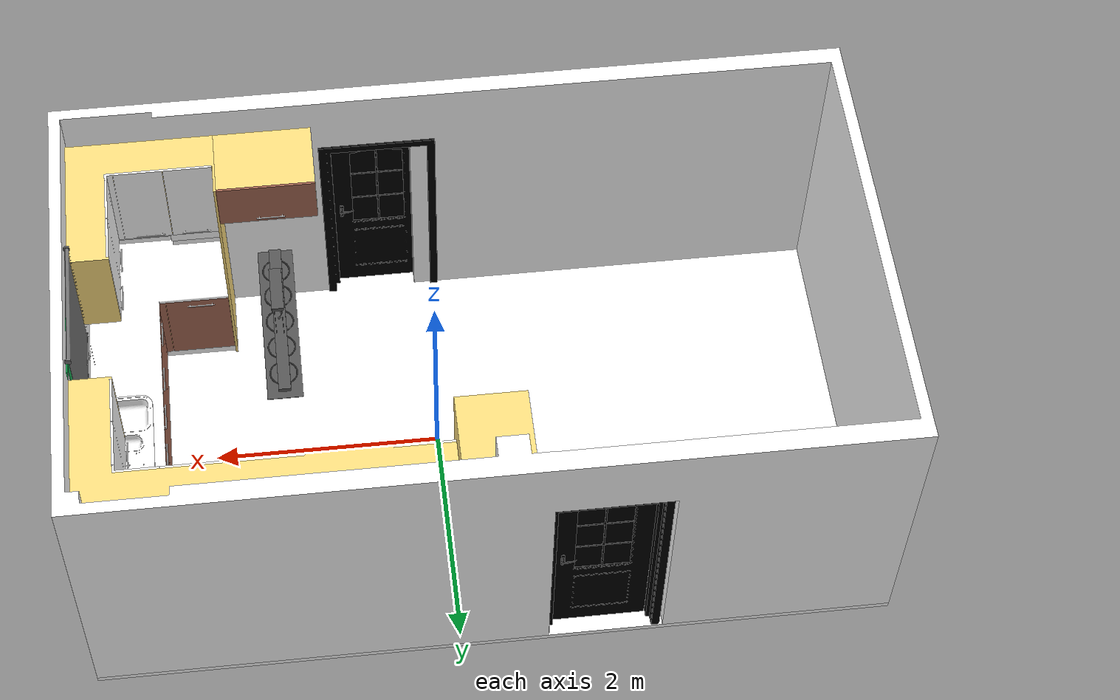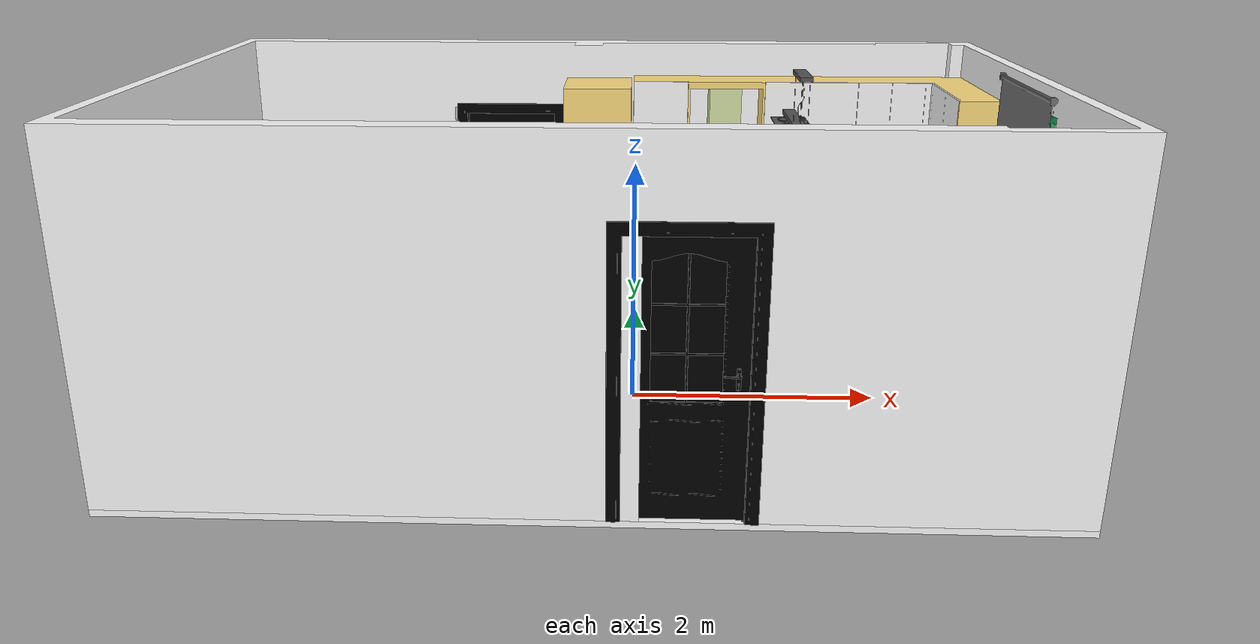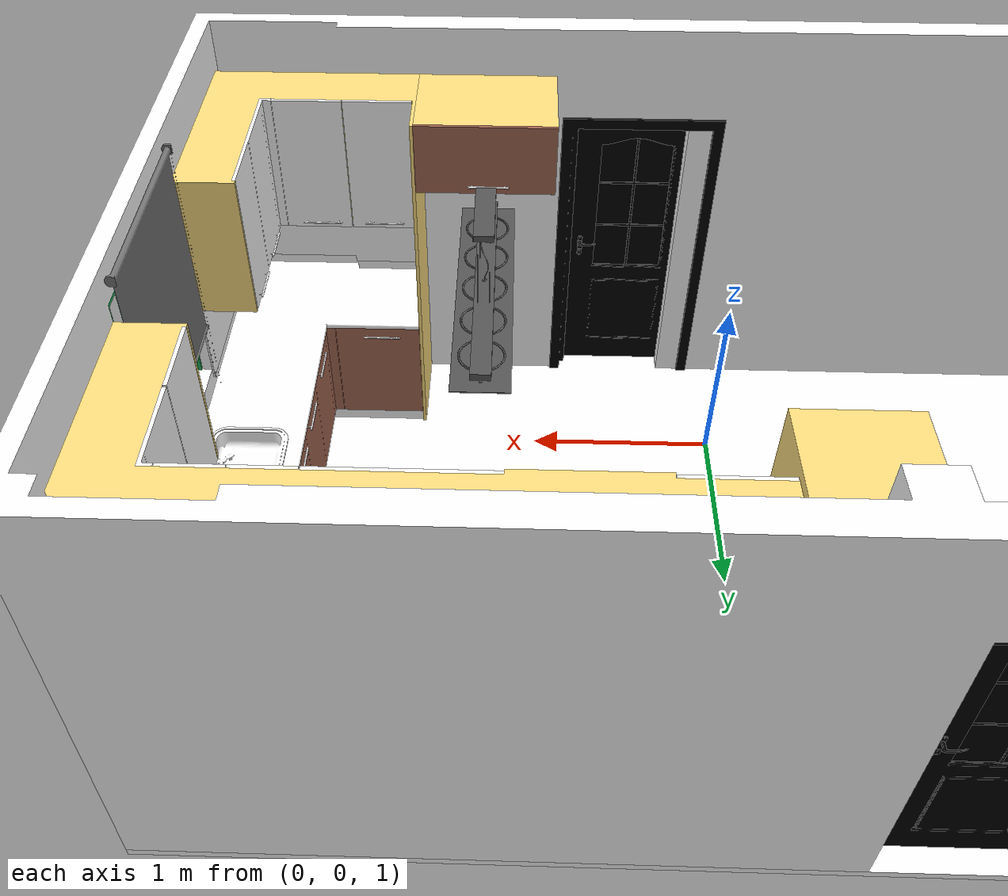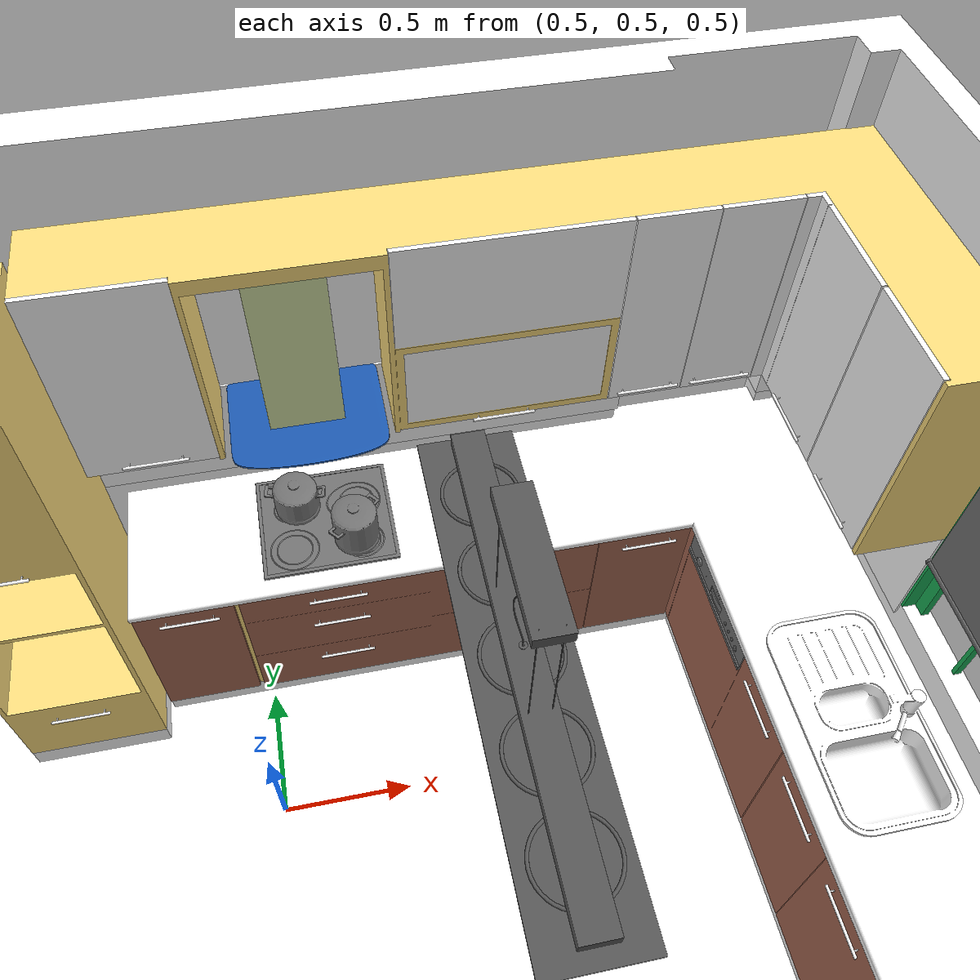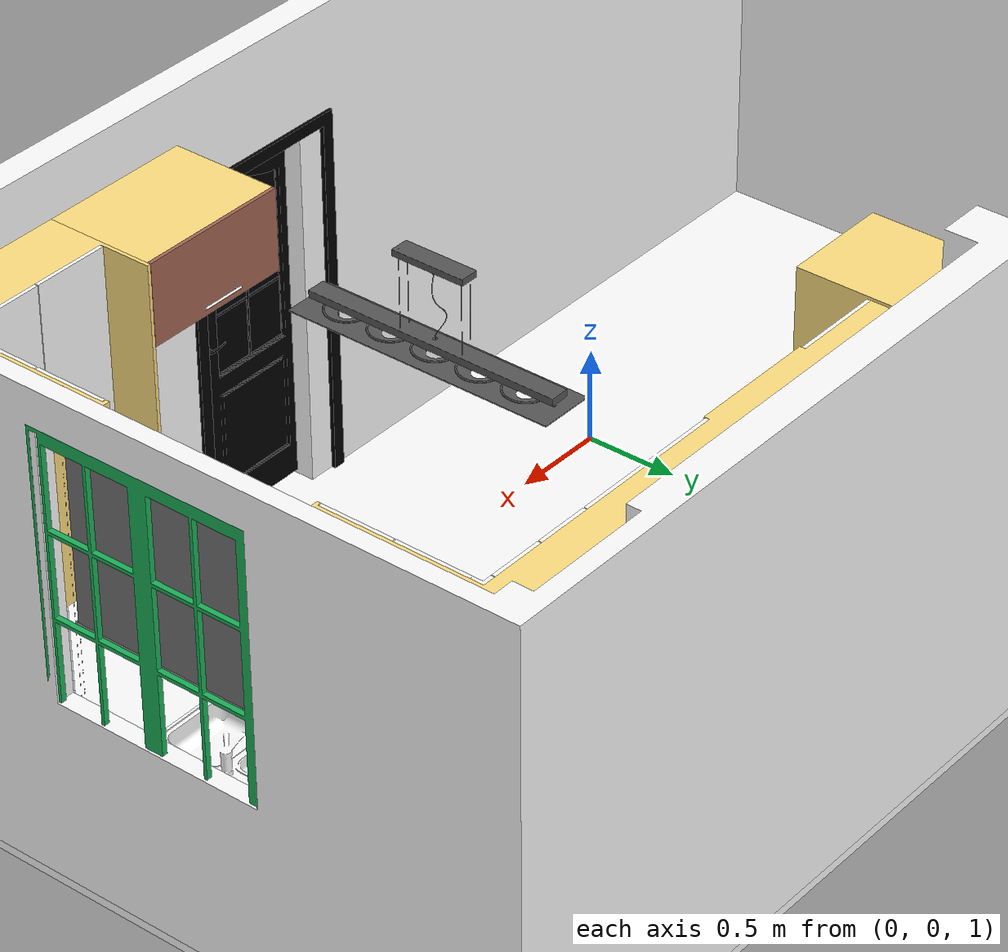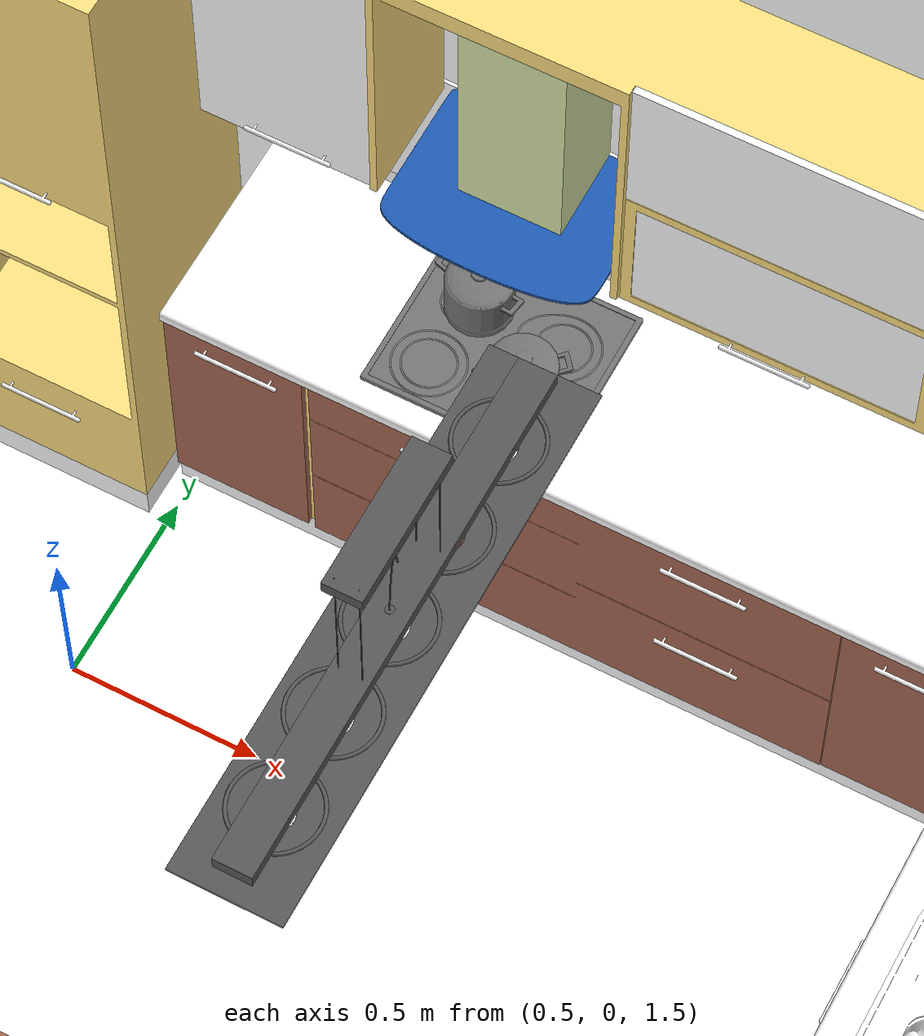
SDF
<sdf version="1.6">
 <world name="default">
  <gravity>0 0 -9.8</gravity>
  <model name="part0.obj">
   <static>1</static>
   <pose>-12.0 -13.9 0 0 0 0</pose>
   <link name="link_d0">
    <inertial>
     <mass>0</mass>
     <inertia>
      <ixx>0.166667</ixx>
      <ixy>0</ixy>
      <ixz>0</ixz>
      <iyy>0.166667</iyy>
      <iyz>0</iyz>
      <izz>0.166667</izz>
     </inertia>
    </inertial>
    <collision concave="yes" name="collision_0">
     <geometry><mesh><scale>.1 .1 .1</scale><uri>fatihrmutfak/part0.obj</uri></mesh></geometry>
    </collision>
    <visual name="visual">
     <geometry><mesh><scale>.1 .1 .1</scale><uri>fatihrmutfak/part0.obj</uri></mesh></geometry>
     <material>
      <ambient>1 0 0 1</ambient>
      <diffuse>0.109800 0.349000 0.694100 1</diffuse>
      <specular>0.1 0.1 0.1 1</specular>
      <emissive>0 0 0 0</emissive>
     </material>
    </visual>
   </link>
  </model>
  <model name="part1.obj">
   <static>1</static>
   <pose>-12.0 -13.9 0 0 0 0</pose>
   <link name="link_d1">
    <inertial>
     <mass>0</mass>
     <inertia>
      <ixx>0.166667</ixx>
      <ixy>0</ixy>
      <ixz>0</ixz>
      <iyy>0.166667</iyy>
      <iyz>0</iyz>
      <izz>0.166667</izz>
     </inertia>
    </inertial>
    <collision concave="yes" name="collision_1">
     <geometry><mesh><scale>.1 .1 .1</scale><uri>fatihrmutfak/part1.obj</uri></mesh></geometry>
    </collision>
    <visual name="visual">
     <geometry><mesh><scale>.1 .1 .1</scale><uri>fatihrmutfak/part1.obj</uri></mesh></geometry>
     <material>
      <ambient>1 0 0 1</ambient>
      <diffuse>0.839200 0.898000 0.651000 1</diffuse>
      <specular>0.1 0.1 0.1 1</specular>
      <emissive>0 0 0 0</emissive>
     </material>
    </visual>
   </link>
  </model>
  <model name="part2.obj">
   <static>1</static>
   <pose>-12.0 -13.9 0 0 0 0</pose>
   <link name="link_d2">
    <inertial>
     <mass>0</mass>
     <inertia>
      <ixx>0.166667</ixx>
      <ixy>0</ixy>
      <ixz>0</ixz>
      <iyy>0.166667</iyy>
      <iyz>0</iyz>
      <izz>0.166667</izz>
     </inertia>
    </inertial>
    <collision concave="yes" name="collision_2">
     <geometry><mesh><scale>.1 .1 .1</scale><uri>fatihrmutfak/part2.obj</uri></mesh></geometry>
    </collision>
    <visual name="visual">
     <geometry><mesh><scale>.1 .1 .1</scale><uri>fatihrmutfak/part2.obj</uri></mesh></geometry>
     <material>
      <ambient>1 0 0 1</ambient>
      <diffuse>0.698000 0.000000 0.000000 1</diffuse>
      <specular>0.1 0.1 0.1 1</specular>
      <emissive>0 0 0 0</emissive>
     </material>
    </visual>
   </link>
  </model>
  <model name="part3.obj">
   <static>1</static>
   <pose>-12.0 -13.9 0 0 0 0</pose>
   <link name="link_d3">
    <inertial>
     <mass>0</mass>
     <inertia>
      <ixx>0.166667</ixx>
      <ixy>0</ixy>
      <ixz>0</ixz>
      <iyy>0.166667</iyy>
      <iyz>0</iyz>
      <izz>0.166667</izz>
     </inertia>
    </inertial>
    <collision concave="yes" name="collision_3">
     <geometry><mesh><scale>.1 .1 .1</scale><uri>fatihrmutfak/part3.obj</uri></mesh></geometry>
    </collision>
    <visual name="visual">
     <geometry><mesh><scale>.1 .1 .1</scale><uri>fatihrmutfak/part3.obj</uri></mesh></geometry>
     <material>
      <ambient>1 0 0 1</ambient>
      <diffuse>0.698000 0.000000 0.000000 1</diffuse>
      <specular>0.1 0.1 0.1 1</specular>
      <emissive>0 0 0 0</emissive>
     </material>
    </visual>
   </link>
  </model>
  <model name="part4.obj">
   <static>1</static>
   <pose>-12.0 -13.9 0 0 0 0</pose>
   <link name="link_d4">
    <inertial>
     <mass>0</mass>
     <inertia>
      <ixx>0.166667</ixx>
      <ixy>0</ixy>
      <ixz>0</ixz>
      <iyy>0.166667</iyy>
      <iyz>0</iyz>
      <izz>0.166667</izz>
     </inertia>
    </inertial>
    <collision concave="yes" name="collision_4">
     <geometry><mesh><scale>.1 .1 .1</scale><uri>fatihrmutfak/part4.obj</uri></mesh></geometry>
    </collision>
    <visual name="visual">
     <geometry><mesh><scale>.1 .1 .1</scale><uri>fatihrmutfak/part4.obj</uri></mesh></geometry>
     <material>
      <ambient>1 0 0 1</ambient>
      <diffuse>0.698000 0.000000 0.000000 1</diffuse>
      <specular>0.1 0.1 0.1 1</specular>
      <emissive>0 0 0 0</emissive>
     </material>
    </visual>
   </link>
  </model>
  <model name="part5.obj">
   <static>1</static>
   <pose>-12.0 -13.9 0 0 0 0</pose>
   <link name="link_d5">
    <inertial>
     <mass>0</mass>
     <inertia>
      <ixx>0.166667</ixx>
      <ixy>0</ixy>
      <ixz>0</ixz>
      <iyy>0.166667</iyy>
      <iyz>0</iyz>
      <izz>0.166667</izz>
     </inertia>
    </inertial>
    <collision concave="yes" name="collision_5">
     <geometry><mesh><scale>.1 .1 .1</scale><uri>fatihrmutfak/part5.obj</uri></mesh></geometry>
    </collision>
    <visual name="visual">
     <geometry><mesh><scale>.1 .1 .1</scale><uri>fatihrmutfak/part5.obj</uri></mesh></geometry>
     <material>
      <ambient>1 0 0 1</ambient>
      <diffuse>0.698000 0.000000 0.000000 1</diffuse>
      <specular>0.1 0.1 0.1 1</specular>
      <emissive>0 0 0 0</emissive>
     </material>
    </visual>
   </link>
  </model>
  <model name="part6.obj">
   <static>1</static>
   <pose>-12.0 -13.9 0 0 0 0</pose>
   <link name="link_d6">
    <inertial>
     <mass>0</mass>
     <inertia>
      <ixx>0.166667</ixx>
      <ixy>0</ixy>
      <ixz>0</ixz>
      <iyy>0.166667</iyy>
      <iyz>0</iyz>
      <izz>0.166667</izz>
     </inertia>
    </inertial>
    <collision concave="yes" name="collision_6">
     <geometry><mesh><scale>.1 .1 .1</scale><uri>fatihrmutfak/part6.obj</uri></mesh></geometry>
    </collision>
    <visual name="visual">
     <geometry><mesh><scale>.1 .1 .1</scale><uri>fatihrmutfak/part6.obj</uri></mesh></geometry>
     <material>
      <ambient>1 0 0 1</ambient>
      <diffuse>0.698000 0.000000 0.000000 1</diffuse>
      <specular>0.1 0.1 0.1 1</specular>
      <emissive>0 0 0 0</emissive>
     </material>
    </visual>
   </link>
  </model>
  <model name="part7.obj">
   <static>1</static>
   <pose>-12.0 -13.9 0 0 0 0</pose>
   <link name="link_d7">
    <inertial>
     <mass>0</mass>
     <inertia>
      <ixx>0.166667</ixx>
      <ixy>0</ixy>
      <ixz>0</ixz>
      <iyy>0.166667</iyy>
      <iyz>0</iyz>
      <izz>0.166667</izz>
     </inertia>
    </inertial>
    <collision concave="yes" name="collision_7">
     <geometry><mesh><scale>.1 .1 .1</scale><uri>fatihrmutfak/part7.obj</uri></mesh></geometry>
    </collision>
    <visual name="visual">
     <geometry><mesh><scale>.1 .1 .1</scale><uri>fatihrmutfak/part7.obj</uri></mesh></geometry>
     <material>
      <ambient>1 0 0 1</ambient>
      <diffuse>0.698000 0.000000 0.000000 1</diffuse>
      <specular>0.1 0.1 0.1 1</specular>
      <emissive>0 0 0 0</emissive>
     </material>
    </visual>
   </link>
  </model>
  <model name="part8.obj">
   <static>1</static>
   <pose>-12.0 -13.9 0 0 0 0</pose>
   <link name="link_d8">
    <inertial>
     <mass>0</mass>
     <inertia>
      <ixx>0.166667</ixx>
      <ixy>0</ixy>
      <ixz>0</ixz>
      <iyy>0.166667</iyy>
      <iyz>0</iyz>
      <izz>0.166667</izz>
     </inertia>
    </inertial>
    <collision concave="yes" name="collision_8">
     <geometry><mesh><scale>.1 .1 .1</scale><uri>fatihrmutfak/part8.obj</uri></mesh></geometry>
    </collision>
    <visual name="visual">
     <geometry><mesh><scale>.1 .1 .1</scale><uri>fatihrmutfak/part8.obj</uri></mesh></geometry>
     <material>
      <ambient>1 0 0 1</ambient>
      <diffuse>0.698000 0.000000 0.000000 1</diffuse>
      <specular>0.1 0.1 0.1 1</specular>
      <emissive>0 0 0 0</emissive>
     </material>
    </visual>
   </link>
  </model>
  <model name="part9.obj">
   <static>1</static>
   <pose>-12.0 -13.9 0 0 0 0</pose>
   <link name="link_d9">
    <inertial>
     <mass>0</mass>
     <inertia>
      <ixx>0.166667</ixx>
      <ixy>0</ixy>
      <ixz>0</ixz>
      <iyy>0.166667</iyy>
      <iyz>0</iyz>
      <izz>0.166667</izz>
     </inertia>
    </inertial>
    <collision concave="yes" name="collision_9">
     <geometry><mesh><scale>.1 .1 .1</scale><uri>fatihrmutfak/part9.obj</uri></mesh></geometry>
    </collision>
    <visual name="visual">
     <geometry><mesh><scale>.1 .1 .1</scale><uri>fatihrmutfak/part9.obj</uri></mesh></geometry>
     <material>
      <ambient>1 0 0 1</ambient>
      <diffuse>0.698000 0.000000 0.000000 1</diffuse>
      <specular>0.1 0.1 0.1 1</specular>
      <emissive>0 0 0 0</emissive>
     </material>
    </visual>
   </link>
  </model>
  <model name="part10.obj">
   <static>1</static>
   <pose>-12.0 -13.9 0 0 0 0</pose>
   <link name="link_d10">
    <inertial>
     <mass>0</mass>
     <inertia>
      <ixx>0.166667</ixx>
      <ixy>0</ixy>
      <ixz>0</ixz>
      <iyy>0.166667</iyy>
      <iyz>0</iyz>
      <izz>0.166667</izz>
     </inertia>
    </inertial>
    <collision concave="yes" name="collision_10">
     <geometry><mesh><scale>.1 .1 .1</scale><uri>fatihrmutfak/part10.obj</uri></mesh></geometry>
    </collision>
    <visual name="visual">
     <geometry><mesh><scale>.1 .1 .1</scale><uri>fatihrmutfak/part10.obj</uri></mesh></geometry>
     <material>
      <ambient>1 0 0 1</ambient>
      <diffuse>0.058800 0.058800 0.058800 1</diffuse>
      <specular>0.1 0.1 0.1 1</specular>
      <emissive>0 0 0 0</emissive>
     </material>
    </visual>
   </link>
  </model>
  <model name="part11.obj">
   <static>1</static>
   <pose>-12.0 -13.9 0 0 0 0</pose>
   <link name="link_d11">
    <inertial>
     <mass>0</mass>
     <inertia>
      <ixx>0.166667</ixx>
      <ixy>0</ixy>
      <ixz>0</ixz>
      <iyy>0.166667</iyy>
      <iyz>0</iyz>
      <izz>0.166667</izz>
     </inertia>
    </inertial>
    <collision concave="yes" name="collision_11">
     <geometry><mesh><scale>.1 .1 .1</scale><uri>fatihrmutfak/part11.obj</uri></mesh></geometry>
    </collision>
    <visual name="visual">
     <geometry><mesh><scale>.1 .1 .1</scale><uri>fatihrmutfak/part11.obj</uri></mesh></geometry>
     <material>
      <ambient>1 0 0 1</ambient>
      <diffuse>0.058800 0.058800 0.058800 1</diffuse>
      <specular>0.1 0.1 0.1 1</specular>
      <emissive>0 0 0 0</emissive>
     </material>
    </visual>
   </link>
  </model>
  <model name="part12.obj">
   <static>1</static>
   <pose>-12.0 -13.9 0 0 0 0</pose>
   <link name="link_d12">
    <inertial>
     <mass>0</mass>
     <inertia>
      <ixx>0.166667</ixx>
      <ixy>0</ixy>
      <ixz>0</ixz>
      <iyy>0.166667</iyy>
      <iyz>0</iyz>
      <izz>0.166667</izz>
     </inertia>
    </inertial>
    <collision concave="yes" name="collision_12">
     <geometry><mesh><scale>.1 .1 .1</scale><uri>fatihrmutfak/part12.obj</uri></mesh></geometry>
    </collision>
    <visual name="visual">
     <geometry><mesh><scale>.1 .1 .1</scale><uri>fatihrmutfak/part12.obj</uri></mesh></geometry>
     <material>
      <ambient>1 0 0 1</ambient>
      <diffuse>0.058800 0.058800 0.058800 1</diffuse>
      <specular>0.1 0.1 0.1 1</specular>
      <emissive>0 0 0 0</emissive>
     </material>
    </visual>
   </link>
  </model>
  <model name="part13.obj">
   <static>1</static>
   <pose>-12.0 -13.9 0 0 0 0</pose>
   <link name="link_d13">
    <inertial>
     <mass>0</mass>
     <inertia>
      <ixx>0.166667</ixx>
      <ixy>0</ixy>
      <ixz>0</ixz>
      <iyy>0.166667</iyy>
      <iyz>0</iyz>
      <izz>0.166667</izz>
     </inertia>
    </inertial>
    <collision concave="yes" name="collision_13">
     <geometry><mesh><scale>.1 .1 .1</scale><uri>fatihrmutfak/part13.obj</uri></mesh></geometry>
    </collision>
    <visual name="visual">
     <geometry><mesh><scale>.1 .1 .1</scale><uri>fatihrmutfak/part13.obj</uri></mesh></geometry>
     <material>
      <ambient>1 0 0 1</ambient>
      <diffuse>0.058800 0.058800 0.058800 1</diffuse>
      <specular>0.1 0.1 0.1 1</specular>
      <emissive>0 0 0 0</emissive>
     </material>
    </visual>
   </link>
  </model>
  <model name="part14.obj">
   <static>1</static>
   <pose>-12.0 -13.9 0 0 0 0</pose>
   <link name="link_d14">
    <inertial>
     <mass>0</mass>
     <inertia>
      <ixx>0.166667</ixx>
      <ixy>0</ixy>
      <ixz>0</ixz>
      <iyy>0.166667</iyy>
      <iyz>0</iyz>
      <izz>0.166667</izz>
     </inertia>
    </inertial>
    <collision concave="yes" name="collision_14">
     <geometry><mesh><scale>.1 .1 .1</scale><uri>fatihrmutfak/part14.obj</uri></mesh></geometry>
    </collision>
    <visual name="visual">
     <geometry><mesh><scale>.1 .1 .1</scale><uri>fatihrmutfak/part14.obj</uri></mesh></geometry>
     <material>
      <ambient>1 0 0 1</ambient>
      <diffuse>0.451000 0.451000 0.451000 1</diffuse>
      <specular>0.1 0.1 0.1 1</specular>
      <emissive>0 0 0 0</emissive>
     </material>
    </visual>
   </link>
  </model>
  <model name="part15.obj">
   <static>1</static>
   <pose>-12.0 -13.9 0 0 0 0</pose>
   <link name="link_d15">
    <inertial>
     <mass>0</mass>
     <inertia>
      <ixx>0.166667</ixx>
      <ixy>0</ixy>
      <ixz>0</ixz>
      <iyy>0.166667</iyy>
      <iyz>0</iyz>
      <izz>0.166667</izz>
     </inertia>
    </inertial>
    <collision concave="yes" name="collision_15">
     <geometry><mesh><scale>.1 .1 .1</scale><uri>fatihrmutfak/part15.obj</uri></mesh></geometry>
    </collision>
    <visual name="visual">
     <geometry><mesh><scale>.1 .1 .1</scale><uri>fatihrmutfak/part15.obj</uri></mesh></geometry>
     <material>
      <ambient>1 0 0 1</ambient>
      <diffuse>0.451000 0.451000 0.451000 1</diffuse>
      <specular>0.1 0.1 0.1 1</specular>
      <emissive>0 0 0 0</emissive>
     </material>
    </visual>
   </link>
  </model>
  <model name="part16.obj">
   <static>1</static>
   <pose>-12.0 -13.9 0 0 0 0</pose>
   <link name="link_d16">
    <inertial>
     <mass>0</mass>
     <inertia>
      <ixx>0.166667</ixx>
      <ixy>0</ixy>
      <ixz>0</ixz>
      <iyy>0.166667</iyy>
      <iyz>0</iyz>
      <izz>0.166667</izz>
     </inertia>
    </inertial>
    <collision concave="yes" name="collision_16">
     <geometry><mesh><scale>.1 .1 .1</scale><uri>fatihrmutfak/part16.obj</uri></mesh></geometry>
    </collision>
    <visual name="visual">
     <geometry><mesh><scale>.1 .1 .1</scale><uri>fatihrmutfak/part16.obj</uri></mesh></geometry>
     <material>
      <ambient>1 0 0 1</ambient>
      <diffuse>0.451000 0.451000 0.451000 1</diffuse>
      <specular>0.1 0.1 0.1 1</specular>
      <emissive>0 0 0 0</emissive>
     </material>
    </visual>
   </link>
  </model>
  <model name="part17.obj">
   <static>1</static>
   <pose>-12.0 -13.9 0 0 0 0</pose>
   <link name="link_d17">
    <inertial>
     <mass>0</mass>
     <inertia>
      <ixx>0.166667</ixx>
      <ixy>0</ixy>
      <ixz>0</ixz>
      <iyy>0.166667</iyy>
      <iyz>0</iyz>
      <izz>0.166667</izz>
     </inertia>
    </inertial>
    <collision concave="yes" name="collision_17">
     <geometry><mesh><scale>.1 .1 .1</scale><uri>fatihrmutfak/part17.obj</uri></mesh></geometry>
    </collision>
    <visual name="visual">
     <geometry><mesh><scale>.1 .1 .1</scale><uri>fatihrmutfak/part17.obj</uri></mesh></geometry>
     <material>
      <ambient>1 0 0 1</ambient>
      <diffuse>0.451000 0.451000 0.451000 1</diffuse>
      <specular>0.1 0.1 0.1 1</specular>
      <emissive>0 0 0 0</emissive>
     </material>
    </visual>
   </link>
  </model>
  <model name="part18.obj">
   <static>1</static>
   <pose>-12.0 -13.9 0 0 0 0</pose>
   <link name="link_d18">
    <inertial>
     <mass>0</mass>
     <inertia>
      <ixx>0.166667</ixx>
      <ixy>0</ixy>
      <ixz>0</ixz>
      <iyy>0.166667</iyy>
      <iyz>0</iyz>
      <izz>0.166667</izz>
     </inertia>
    </inertial>
    <collision concave="yes" name="collision_18">
     <geometry><mesh><scale>.1 .1 .1</scale><uri>fatihrmutfak/part18.obj</uri></mesh></geometry>
    </collision>
    <visual name="visual">
     <geometry><mesh><scale>.1 .1 .1</scale><uri>fatihrmutfak/part18.obj</uri></mesh></geometry>
     <material>
      <ambient>1 0 0 1</ambient>
      <diffuse>0.451000 0.451000 0.451000 1</diffuse>
      <specular>0.1 0.1 0.1 1</specular>
      <emissive>0 0 0 0</emissive>
     </material>
    </visual>
   </link>
  </model>
  <model name="part19.obj">
   <static>1</static>
   <pose>-12.0 -13.9 0 0 0 0</pose>
   <link name="link_d19">
    <inertial>
     <mass>0</mass>
     <inertia>
      <ixx>0.166667</ixx>
      <ixy>0</ixy>
      <ixz>0</ixz>
      <iyy>0.166667</iyy>
      <iyz>0</iyz>
      <izz>0.166667</izz>
     </inertia>
    </inertial>
    <collision concave="yes" name="collision_19">
     <geometry><mesh><scale>.1 .1 .1</scale><uri>fatihrmutfak/part19.obj</uri></mesh></geometry>
    </collision>
    <visual name="visual">
     <geometry><mesh><scale>.1 .1 .1</scale><uri>fatihrmutfak/part19.obj</uri></mesh></geometry>
     <material>
      <ambient>1 0 0 1</ambient>
      <diffuse>0.451000 0.451000 0.451000 1</diffuse>
      <specular>0.1 0.1 0.1 1</specular>
      <emissive>0 0 0 0</emissive>
     </material>
    </visual>
   </link>
  </model>
  <model name="part20.obj">
   <static>1</static>
   <pose>-12.0 -13.9 0 0 0 0</pose>
   <link name="link_d20">
    <inertial>
     <mass>0</mass>
     <inertia>
      <ixx>0.166667</ixx>
      <ixy>0</ixy>
      <ixz>0</ixz>
      <iyy>0.166667</iyy>
      <iyz>0</iyz>
      <izz>0.166667</izz>
     </inertia>
    </inertial>
    <collision concave="yes" name="collision_20">
     <geometry><mesh><scale>.1 .1 .1</scale><uri>fatihrmutfak/part20.obj</uri></mesh></geometry>
    </collision>
    <visual name="visual">
     <geometry><mesh><scale>.1 .1 .1</scale><uri>fatihrmutfak/part20.obj</uri></mesh></geometry>
     <material>
      <ambient>1 0 0 1</ambient>
      <diffuse>0.451000 0.451000 0.451000 1</diffuse>
      <specular>0.1 0.1 0.1 1</specular>
      <emissive>0 0 0 0</emissive>
     </material>
    </visual>
   </link>
  </model>
  <model name="part21.obj">
   <static>1</static>
   <pose>-12.0 -13.9 0 0 0 0</pose>
   <link name="link_d21">
    <inertial>
     <mass>0</mass>
     <inertia>
      <ixx>0.166667</ixx>
      <ixy>0</ixy>
      <ixz>0</ixz>
      <iyy>0.166667</iyy>
      <iyz>0</iyz>
      <izz>0.166667</izz>
     </inertia>
    </inertial>
    <collision concave="yes" name="collision_21">
     <geometry><mesh><scale>.1 .1 .1</scale><uri>fatihrmutfak/part21.obj</uri></mesh></geometry>
    </collision>
    <visual name="visual">
     <geometry><mesh><scale>.1 .1 .1</scale><uri>fatihrmutfak/part21.obj</uri></mesh></geometry>
     <material>
      <ambient>1 0 0 1</ambient>
      <diffuse>0.451000 0.451000 0.451000 1</diffuse>
      <specular>0.1 0.1 0.1 1</specular>
      <emissive>0 0 0 0</emissive>
     </material>
    </visual>
   </link>
  </model>
  <model name="part22.obj">
   <static>1</static>
   <pose>-12.0 -13.9 0 0 0 0</pose>
   <link name="link_d22">
    <inertial>
     <mass>0</mass>
     <inertia>
      <ixx>0.166667</ixx>
      <ixy>0</ixy>
      <ixz>0</ixz>
      <iyy>0.166667</iyy>
      <iyz>0</iyz>
      <izz>0.166667</izz>
     </inertia>
    </inertial>
    <collision concave="yes" name="collision_22">
     <geometry><mesh><scale>.1 .1 .1</scale><uri>fatihrmutfak/part22.obj</uri></mesh></geometry>
    </collision>
    <visual name="visual">
     <geometry><mesh><scale>.1 .1 .1</scale><uri>fatihrmutfak/part22.obj</uri></mesh></geometry>
     <material>
      <ambient>1 0 0 1</ambient>
      <diffuse>0.451000 0.451000 0.451000 1</diffuse>
      <specular>0.1 0.1 0.1 1</specular>
      <emissive>0 0 0 0</emissive>
     </material>
    </visual>
   </link>
  </model>
  <model name="part23.obj">
   <static>1</static>
   <pose>-12.0 -13.9 0 0 0 0</pose>
   <link name="link_d23">
    <inertial>
     <mass>0</mass>
     <inertia>
      <ixx>0.166667</ixx>
      <ixy>0</ixy>
      <ixz>0</ixz>
      <iyy>0.166667</iyy>
      <iyz>0</iyz>
      <izz>0.166667</izz>
     </inertia>
    </inertial>
    <collision concave="yes" name="collision_23">
     <geometry><mesh><scale>.1 .1 .1</scale><uri>fatihrmutfak/part23.obj</uri></mesh></geometry>
    </collision>
    <visual name="visual">
     <geometry><mesh><scale>.1 .1 .1</scale><uri>fatihrmutfak/part23.obj</uri></mesh></geometry>
     <material>
      <ambient>1 0 0 1</ambient>
      <diffuse>0.451000 0.451000 0.451000 1</diffuse>
      <specular>0.1 0.1 0.1 1</specular>
      <emissive>0 0 0 0</emissive>
     </material>
    </visual>
   </link>
  </model>
  <model name="part24.obj">
   <static>1</static>
   <pose>-12.0 -13.9 0 0 0 0</pose>
   <link name="link_d24">
    <inertial>
     <mass>0</mass>
     <inertia>
      <ixx>0.166667</ixx>
      <ixy>0</ixy>
      <ixz>0</ixz>
      <iyy>0.166667</iyy>
      <iyz>0</iyz>
      <izz>0.166667</izz>
     </inertia>
    </inertial>
    <collision concave="yes" name="collision_24">
     <geometry><mesh><scale>.1 .1 .1</scale><uri>fatihrmutfak/part24.obj</uri></mesh></geometry>
    </collision>
    <visual name="visual">
     <geometry><mesh><scale>.1 .1 .1</scale><uri>fatihrmutfak/part24.obj</uri></mesh></geometry>
     <material>
      <ambient>1 0 0 1</ambient>
      <diffuse>0.451000 0.451000 0.451000 1</diffuse>
      <specular>0.1 0.1 0.1 1</specular>
      <emissive>0 0 0 0</emissive>
     </material>
    </visual>
   </link>
  </model>
  <model name="part25.obj">
   <static>1</static>
   <pose>-12.0 -13.9 0 0 0 0</pose>
   <link name="link_d25">
    <inertial>
     <mass>0</mass>
     <inertia>
      <ixx>0.166667</ixx>
      <ixy>0</ixy>
      <ixz>0</ixz>
      <iyy>0.166667</iyy>
      <iyz>0</iyz>
      <izz>0.166667</izz>
     </inertia>
    </inertial>
    <collision concave="yes" name="collision_25">
     <geometry><mesh><scale>.1 .1 .1</scale><uri>fatihrmutfak/part25.obj</uri></mesh></geometry>
    </collision>
    <visual name="visual">
     <geometry><mesh><scale>.1 .1 .1</scale><uri>fatihrmutfak/part25.obj</uri></mesh></geometry>
     <material>
      <ambient>1 0 0 1</ambient>
      <diffuse>0.451000 0.451000 0.451000 1</diffuse>
      <specular>0.1 0.1 0.1 1</specular>
      <emissive>0 0 0 0</emissive>
     </material>
    </visual>
   </link>
  </model>
  <model name="part26.obj">
   <static>1</static>
   <pose>-12.0 -13.9 0 0 0 0</pose>
   <link name="link_d26">
    <inertial>
     <mass>0</mass>
     <inertia>
      <ixx>0.166667</ixx>
      <ixy>0</ixy>
      <ixz>0</ixz>
      <iyy>0.166667</iyy>
      <iyz>0</iyz>
      <izz>0.166667</izz>
     </inertia>
    </inertial>
    <collision concave="yes" name="collision_26">
     <geometry><mesh><scale>.1 .1 .1</scale><uri>fatihrmutfak/part26.obj</uri></mesh></geometry>
    </collision>
    <visual name="visual">
     <geometry><mesh><scale>.1 .1 .1</scale><uri>fatihrmutfak/part26.obj</uri></mesh></geometry>
     <material>
      <ambient>1 0 0 1</ambient>
      <diffuse>0.451000 0.451000 0.451000 1</diffuse>
      <specular>0.1 0.1 0.1 1</specular>
      <emissive>0 0 0 0</emissive>
     </material>
    </visual>
   </link>
  </model>
  <model name="part27.obj">
   <static>1</static>
   <pose>-12.0 -13.9 0 0 0 0</pose>
   <link name="link_d27">
    <inertial>
     <mass>0</mass>
     <inertia>
      <ixx>0.166667</ixx>
      <ixy>0</ixy>
      <ixz>0</ixz>
      <iyy>0.166667</iyy>
      <iyz>0</iyz>
      <izz>0.166667</izz>
     </inertia>
    </inertial>
    <collision concave="yes" name="collision_27">
     <geometry><mesh><scale>.1 .1 .1</scale><uri>fatihrmutfak/part27.obj</uri></mesh></geometry>
    </collision>
    <visual name="visual">
     <geometry><mesh><scale>.1 .1 .1</scale><uri>fatihrmutfak/part27.obj</uri></mesh></geometry>
     <material>
      <ambient>1 0 0 1</ambient>
      <diffuse>0.451000 0.451000 0.451000 1</diffuse>
      <specular>0.1 0.1 0.1 1</specular>
      <emissive>0 0 0 0</emissive>
     </material>
    </visual>
   </link>
  </model>
  <model name="part28.obj">
   <static>1</static>
   <pose>-12.0 -13.9 0 0 0 0</pose>
   <link name="link_d28">
    <inertial>
     <mass>0</mass>
     <inertia>
      <ixx>0.166667</ixx>
      <ixy>0</ixy>
      <ixz>0</ixz>
      <iyy>0.166667</iyy>
      <iyz>0</iyz>
      <izz>0.166667</izz>
     </inertia>
    </inertial>
    <collision concave="yes" name="collision_28">
     <geometry><mesh><scale>.1 .1 .1</scale><uri>fatihrmutfak/part28.obj</uri></mesh></geometry>
    </collision>
    <visual name="visual">
     <geometry><mesh><scale>.1 .1 .1</scale><uri>fatihrmutfak/part28.obj</uri></mesh></geometry>
     <material>
      <ambient>1 0 0 1</ambient>
      <diffuse>0.341200 0.878400 0.776500 1</diffuse>
      <specular>0.1 0.1 0.1 1</specular>
      <emissive>0 0 0 0</emissive>
     </material>
    </visual>
   </link>
  </model>
  <model name="part29.obj">
   <static>1</static>
   <pose>-12.0 -13.9 0 0 0 0</pose>
   <link name="link_d29">
    <inertial>
     <mass>0</mass>
     <inertia>
      <ixx>0.166667</ixx>
      <ixy>0</ixy>
      <ixz>0</ixz>
      <iyy>0.166667</iyy>
      <iyz>0</iyz>
      <izz>0.166667</izz>
     </inertia>
    </inertial>
    <collision concave="yes" name="collision_29">
     <geometry><mesh><scale>.1 .1 .1</scale><uri>fatihrmutfak/part29.obj</uri></mesh></geometry>
    </collision>
    <visual name="visual">
     <geometry><mesh><scale>.1 .1 .1</scale><uri>fatihrmutfak/part29.obj</uri></mesh></geometry>
     <material>
      <ambient>1 0 0 1</ambient>
      <diffuse>0.341200 0.878400 0.776500 1</diffuse>
      <specular>0.1 0.1 0.1 1</specular>
      <emissive>0 0 0 0</emissive>
     </material>
    </visual>
   </link>
  </model>
  <model name="part30.obj">
   <static>1</static>
   <pose>-12.0 -13.9 0 0 0 0</pose>
   <link name="link_d30">
    <inertial>
     <mass>0</mass>
     <inertia>
      <ixx>0.166667</ixx>
      <ixy>0</ixy>
      <ixz>0</ixz>
      <iyy>0.166667</iyy>
      <iyz>0</iyz>
      <izz>0.166667</izz>
     </inertia>
    </inertial>
    <collision concave="yes" name="collision_30">
     <geometry><mesh><scale>.1 .1 .1</scale><uri>fatihrmutfak/part30.obj</uri></mesh></geometry>
    </collision>
    <visual name="visual">
     <geometry><mesh><scale>.1 .1 .1</scale><uri>fatihrmutfak/part30.obj</uri></mesh></geometry>
     <material>
      <ambient>1 0 0 1</ambient>
      <diffuse>0.341200 0.878400 0.776500 1</diffuse>
      <specular>0.1 0.1 0.1 1</specular>
      <emissive>0 0 0 0</emissive>
     </material>
    </visual>
   </link>
  </model>
  <model name="part31.obj">
   <static>1</static>
   <pose>-12.0 -13.9 0 0 0 0</pose>
   <link name="link_d31">
    <inertial>
     <mass>0</mass>
     <inertia>
      <ixx>0.166667</ixx>
      <ixy>0</ixy>
      <ixz>0</ixz>
      <iyy>0.166667</iyy>
      <iyz>0</iyz>
      <izz>0.166667</izz>
     </inertia>
    </inertial>
    <collision concave="yes" name="collision_31">
     <geometry><mesh><scale>.1 .1 .1</scale><uri>fatihrmutfak/part31.obj</uri></mesh></geometry>
    </collision>
    <visual name="visual">
     <geometry><mesh><scale>.1 .1 .1</scale><uri>fatihrmutfak/part31.obj</uri></mesh></geometry>
     <material>
      <ambient>1 0 0 1</ambient>
      <diffuse>0.341200 0.878400 0.776500 1</diffuse>
      <specular>0.1 0.1 0.1 1</specular>
      <emissive>0 0 0 0</emissive>
     </material>
    </visual>
   </link>
  </model>
  <model name="part32.obj">
   <static>1</static>
   <pose>-12.0 -13.9 0 0 0 0</pose>
   <link name="link_d32">
    <inertial>
     <mass>0</mass>
     <inertia>
      <ixx>0.166667</ixx>
      <ixy>0</ixy>
      <ixz>0</ixz>
      <iyy>0.166667</iyy>
      <iyz>0</iyz>
      <izz>0.166667</izz>
     </inertia>
    </inertial>
    <collision concave="yes" name="collision_32">
     <geometry><mesh><scale>.1 .1 .1</scale><uri>fatihrmutfak/part32.obj</uri></mesh></geometry>
    </collision>
    <visual name="visual">
     <geometry><mesh><scale>.1 .1 .1</scale><uri>fatihrmutfak/part32.obj</uri></mesh></geometry>
     <material>
      <ambient>1 0 0 1</ambient>
      <diffuse>0.341200 0.878400 0.776500 1</diffuse>
      <specular>0.1 0.1 0.1 1</specular>
      <emissive>0 0 0 0</emissive>
     </material>
    </visual>
   </link>
  </model>
  <model name="part33.obj">
   <static>1</static>
   <pose>-12.0 -13.9 0 0 0 0</pose>
   <link name="link_d33">
    <inertial>
     <mass>0</mass>
     <inertia>
      <ixx>0.166667</ixx>
      <ixy>0</ixy>
      <ixz>0</ixz>
      <iyy>0.166667</iyy>
      <iyz>0</iyz>
      <izz>0.166667</izz>
     </inertia>
    </inertial>
    <collision concave="yes" name="collision_33">
     <geometry><mesh><scale>.1 .1 .1</scale><uri>fatihrmutfak/part33.obj</uri></mesh></geometry>
    </collision>
    <visual name="visual">
     <geometry><mesh><scale>.1 .1 .1</scale><uri>fatihrmutfak/part33.obj</uri></mesh></geometry>
     <material>
      <ambient>1 0 0 1</ambient>
      <diffuse>0.341200 0.878400 0.776500 1</diffuse>
      <specular>0.1 0.1 0.1 1</specular>
      <emissive>0 0 0 0</emissive>
     </material>
    </visual>
   </link>
  </model>
  <model name="part34.obj">
   <static>1</static>
   <pose>-12.0 -13.9 0 0 0 0</pose>
   <link name="link_d34">
    <inertial>
     <mass>0</mass>
     <inertia>
      <ixx>0.166667</ixx>
      <ixy>0</ixy>
      <ixz>0</ixz>
      <iyy>0.166667</iyy>
      <iyz>0</iyz>
      <izz>0.166667</izz>
     </inertia>
    </inertial>
    <collision concave="yes" name="collision_34">
     <geometry><mesh><scale>.1 .1 .1</scale><uri>fatihrmutfak/part34.obj</uri></mesh></geometry>
    </collision>
    <visual name="visual">
     <geometry><mesh><scale>.1 .1 .1</scale><uri>fatihrmutfak/part34.obj</uri></mesh></geometry>
     <material>
      <ambient>1 0 0 1</ambient>
      <diffuse>0.337300 0.337300 0.337300 1</diffuse>
      <specular>0.1 0.1 0.1 1</specular>
      <emissive>0 0 0 0</emissive>
     </material>
    </visual>
   </link>
  </model>
  <model name="part35.obj">
   <static>1</static>
   <pose>-12.0 -13.9 0 0 0 0</pose>
   <link name="link_d35">
    <inertial>
     <mass>0</mass>
     <inertia>
      <ixx>0.166667</ixx>
      <ixy>0</ixy>
      <ixz>0</ixz>
      <iyy>0.166667</iyy>
      <iyz>0</iyz>
      <izz>0.166667</izz>
     </inertia>
    </inertial>
    <collision concave="yes" name="collision_35">
     <geometry><mesh><scale>.1 .1 .1</scale><uri>fatihrmutfak/part35.obj</uri></mesh></geometry>
    </collision>
    <visual name="visual">
     <geometry><mesh><scale>.1 .1 .1</scale><uri>fatihrmutfak/part35.obj</uri></mesh></geometry>
     <material>
      <ambient>1 0 0 1</ambient>
      <diffuse>0.337300 0.337300 0.337300 1</diffuse>
      <specular>0.1 0.1 0.1 1</specular>
      <emissive>0 0 0 0</emissive>
     </material>
    </visual>
   </link>
  </model>
  <model name="part36.obj">
   <static>1</static>
   <pose>-12.0 -13.9 0 0 0 0</pose>
   <link name="link_d36">
    <inertial>
     <mass>0</mass>
     <inertia>
      <ixx>0.166667</ixx>
      <ixy>0</ixy>
      <ixz>0</ixz>
      <iyy>0.166667</iyy>
      <iyz>0</iyz>
      <izz>0.166667</izz>
     </inertia>
    </inertial>
    <collision concave="yes" name="collision_36">
     <geometry><mesh><scale>.1 .1 .1</scale><uri>fatihrmutfak/part36.obj</uri></mesh></geometry>
    </collision>
    <visual name="visual">
     <geometry><mesh><scale>.1 .1 .1</scale><uri>fatihrmutfak/part36.obj</uri></mesh></geometry>
     <material>
      <ambient>1 0 0 1</ambient>
      <diffuse>0.337300 0.337300 0.337300 1</diffuse>
      <specular>0.1 0.1 0.1 1</specular>
      <emissive>0 0 0 0</emissive>
     </material>
    </visual>
   </link>
  </model>
  <model name="part37.obj">
   <static>1</static>
   <pose>-12.0 -13.9 0 0 0 0</pose>
   <link name="link_d37">
    <inertial>
     <mass>0</mass>
     <inertia>
      <ixx>0.166667</ixx>
      <ixy>0</ixy>
      <ixz>0</ixz>
      <iyy>0.166667</iyy>
      <iyz>0</iyz>
      <izz>0.166667</izz>
     </inertia>
    </inertial>
    <collision concave="yes" name="collision_37">
     <geometry><mesh><scale>.1 .1 .1</scale><uri>fatihrmutfak/part37.obj</uri></mesh></geometry>
    </collision>
    <visual name="visual">
     <geometry><mesh><scale>.1 .1 .1</scale><uri>fatihrmutfak/part37.obj</uri></mesh></geometry>
     <material>
      <ambient>1 0 0 1</ambient>
      <diffuse>0.337300 0.337300 0.337300 1</diffuse>
      <specular>0.1 0.1 0.1 1</specular>
      <emissive>0 0 0 0</emissive>
     </material>
    </visual>
   </link>
  </model>
  <model name="part38.obj">
   <static>1</static>
   <pose>-12.0 -13.9 0 0 0 0</pose>
   <link name="link_d38">
    <inertial>
     <mass>0</mass>
     <inertia>
      <ixx>0.166667</ixx>
      <ixy>0</ixy>
      <ixz>0</ixz>
      <iyy>0.166667</iyy>
      <iyz>0</iyz>
      <izz>0.166667</izz>
     </inertia>
    </inertial>
    <collision concave="yes" name="collision_38">
     <geometry><mesh><scale>.1 .1 .1</scale><uri>fatihrmutfak/part38.obj</uri></mesh></geometry>
    </collision>
    <visual name="visual">
     <geometry><mesh><scale>.1 .1 .1</scale><uri>fatihrmutfak/part38.obj</uri></mesh></geometry>
     <material>
      <ambient>1 0 0 1</ambient>
      <diffuse>0.337300 0.337300 0.337300 1</diffuse>
      <specular>0.1 0.1 0.1 1</specular>
      <emissive>0 0 0 0</emissive>
     </material>
    </visual>
   </link>
  </model>
  <model name="part39.obj">
   <static>1</static>
   <pose>-12.0 -13.9 0 0 0 0</pose>
   <link name="link_d39">
    <inertial>
     <mass>0</mass>
     <inertia>
      <ixx>0.166667</ixx>
      <ixy>0</ixy>
      <ixz>0</ixz>
      <iyy>0.166667</iyy>
      <iyz>0</iyz>
      <izz>0.166667</izz>
     </inertia>
    </inertial>
    <collision concave="yes" name="collision_39">
     <geometry><mesh><scale>.1 .1 .1</scale><uri>fatihrmutfak/part39.obj</uri></mesh></geometry>
    </collision>
    <visual name="visual">
     <geometry><mesh><scale>.1 .1 .1</scale><uri>fatihrmutfak/part39.obj</uri></mesh></geometry>
     <material>
      <ambient>1 0 0 1</ambient>
      <diffuse>0.337300 0.337300 0.337300 1</diffuse>
      <specular>0.1 0.1 0.1 1</specular>
      <emissive>0 0 0 0</emissive>
     </material>
    </visual>
   </link>
  </model>
  <model name="part40.obj">
   <static>1</static>
   <pose>-12.0 -13.9 0 0 0 0</pose>
   <link name="link_d40">
    <inertial>
     <mass>0</mass>
     <inertia>
      <ixx>0.166667</ixx>
      <ixy>0</ixy>
      <ixz>0</ixz>
      <iyy>0.166667</iyy>
      <iyz>0</iyz>
      <izz>0.166667</izz>
     </inertia>
    </inertial>
    <collision concave="yes" name="collision_40">
     <geometry><mesh><scale>.1 .1 .1</scale><uri>fatihrmutfak/part40.obj</uri></mesh></geometry>
    </collision>
    <visual name="visual">
     <geometry><mesh><scale>.1 .1 .1</scale><uri>fatihrmutfak/part40.obj</uri></mesh></geometry>
     <material>
      <ambient>1 0 0 1</ambient>
      <diffuse>0.337300 0.337300 0.337300 1</diffuse>
      <specular>0.1 0.1 0.1 1</specular>
      <emissive>0 0 0 0</emissive>
     </material>
    </visual>
   </link>
  </model>
  <model name="part41.obj">
   <static>1</static>
   <pose>-12.0 -13.9 0 0 0 0</pose>
   <link name="link_d41">
    <inertial>
     <mass>0</mass>
     <inertia>
      <ixx>0.166667</ixx>
      <ixy>0</ixy>
      <ixz>0</ixz>
      <iyy>0.166667</iyy>
      <iyz>0</iyz>
      <izz>0.166667</izz>
     </inertia>
    </inertial>
    <collision concave="yes" name="collision_41">
     <geometry><mesh><scale>.1 .1 .1</scale><uri>fatihrmutfak/part41.obj</uri></mesh></geometry>
    </collision>
    <visual name="visual">
     <geometry><mesh><scale>.1 .1 .1</scale><uri>fatihrmutfak/part41.obj</uri></mesh></geometry>
     <material>
      <ambient>1 0 0 1</ambient>
      <diffuse>0.337300 0.337300 0.337300 1</diffuse>
      <specular>0.1 0.1 0.1 1</specular>
      <emissive>0 0 0 0</emissive>
     </material>
    </visual>
   </link>
  </model>
  <model name="part42.obj">
   <static>1</static>
   <pose>-12.0 -13.9 0 0 0 0</pose>
   <link name="link_d42">
    <inertial>
     <mass>0</mass>
     <inertia>
      <ixx>0.166667</ixx>
      <ixy>0</ixy>
      <ixz>0</ixz>
      <iyy>0.166667</iyy>
      <iyz>0</iyz>
      <izz>0.166667</izz>
     </inertia>
    </inertial>
    <collision concave="yes" name="collision_42">
     <geometry><mesh><scale>.1 .1 .1</scale><uri>fatihrmutfak/part42.obj</uri></mesh></geometry>
    </collision>
    <visual name="visual">
     <geometry><mesh><scale>.1 .1 .1</scale><uri>fatihrmutfak/part42.obj</uri></mesh></geometry>
     <material>
      <ambient>1 0 0 1</ambient>
      <diffuse>0.337300 0.337300 0.337300 1</diffuse>
      <specular>0.1 0.1 0.1 1</specular>
      <emissive>0 0 0 0</emissive>
     </material>
    </visual>
   </link>
  </model>
  <model name="part43.obj">
   <static>1</static>
   <pose>-12.0 -13.9 0 0 0 0</pose>
   <link name="link_d43">
    <inertial>
     <mass>0</mass>
     <inertia>
      <ixx>0.166667</ixx>
      <ixy>0</ixy>
      <ixz>0</ixz>
      <iyy>0.166667</iyy>
      <iyz>0</iyz>
      <izz>0.166667</izz>
     </inertia>
    </inertial>
    <collision concave="yes" name="collision_43">
     <geometry><mesh><scale>.1 .1 .1</scale><uri>fatihrmutfak/part43.obj</uri></mesh></geometry>
    </collision>
    <visual name="visual">
     <geometry><mesh><scale>.1 .1 .1</scale><uri>fatihrmutfak/part43.obj</uri></mesh></geometry>
     <material>
      <ambient>1 0 0 1</ambient>
      <diffuse>0.337300 0.337300 0.337300 1</diffuse>
      <specular>0.1 0.1 0.1 1</specular>
      <emissive>0 0 0 0</emissive>
     </material>
    </visual>
   </link>
  </model>
  <model name="part44.obj">
   <static>1</static>
   <pose>-12.0 -13.9 0 0 0 0</pose>
   <link name="link_d44">
    <inertial>
     <mass>0</mass>
     <inertia>
      <ixx>0.166667</ixx>
      <ixy>0</ixy>
      <ixz>0</ixz>
      <iyy>0.166667</iyy>
      <iyz>0</iyz>
      <izz>0.166667</izz>
     </inertia>
    </inertial>
    <collision concave="yes" name="collision_44">
     <geometry><mesh><scale>.1 .1 .1</scale><uri>fatihrmutfak/part44.obj</uri></mesh></geometry>
    </collision>
    <visual name="visual">
     <geometry><mesh><scale>.1 .1 .1</scale><uri>fatihrmutfak/part44.obj</uri></mesh></geometry>
     <material>
      <ambient>1 0 0 1</ambient>
      <diffuse>0.337300 0.337300 0.337300 1</diffuse>
      <specular>0.1 0.1 0.1 1</specular>
      <emissive>0 0 0 0</emissive>
     </material>
    </visual>
   </link>
  </model>
  <model name="part45.obj">
   <static>1</static>
   <pose>-12.0 -13.9 0 0 0 0</pose>
   <link name="link_d45">
    <inertial>
     <mass>0</mass>
     <inertia>
      <ixx>0.166667</ixx>
      <ixy>0</ixy>
      <ixz>0</ixz>
      <iyy>0.166667</iyy>
      <iyz>0</iyz>
      <izz>0.166667</izz>
     </inertia>
    </inertial>
    <collision concave="yes" name="collision_45">
     <geometry><mesh><scale>.1 .1 .1</scale><uri>fatihrmutfak/part45.obj</uri></mesh></geometry>
    </collision>
    <visual name="visual">
     <geometry><mesh><scale>.1 .1 .1</scale><uri>fatihrmutfak/part45.obj</uri></mesh></geometry>
     <material>
      <ambient>1 0 0 1</ambient>
      <diffuse>0.337300 0.337300 0.337300 1</diffuse>
      <specular>0.1 0.1 0.1 1</specular>
      <emissive>0 0 0 0</emissive>
     </material>
    </visual>
   </link>
  </model>
  <model name="part46.obj">
   <static>1</static>
   <pose>-12.0 -13.9 0 0 0 0</pose>
   <link name="link_d46">
    <inertial>
     <mass>0</mass>
     <inertia>
      <ixx>0.166667</ixx>
      <ixy>0</ixy>
      <ixz>0</ixz>
      <iyy>0.166667</iyy>
      <iyz>0</iyz>
      <izz>0.166667</izz>
     </inertia>
    </inertial>
    <collision concave="yes" name="collision_46">
     <geometry><mesh><scale>.1 .1 .1</scale><uri>fatihrmutfak/part46.obj</uri></mesh></geometry>
    </collision>
    <visual name="visual">
     <geometry><mesh><scale>.1 .1 .1</scale><uri>fatihrmutfak/part46.obj</uri></mesh></geometry>
     <material>
      <ambient>1 0 0 1</ambient>
      <diffuse>0.337300 0.337300 0.337300 1</diffuse>
      <specular>0.1 0.1 0.1 1</specular>
      <emissive>0 0 0 0</emissive>
     </material>
    </visual>
   </link>
  </model>
  <model name="part47.obj">
   <static>1</static>
   <pose>-12.0 -13.9 0 0 0 0</pose>
   <link name="link_d47">
    <inertial>
     <mass>0</mass>
     <inertia>
      <ixx>0.166667</ixx>
      <ixy>0</ixy>
      <ixz>0</ixz>
      <iyy>0.166667</iyy>
      <iyz>0</iyz>
      <izz>0.166667</izz>
     </inertia>
    </inertial>
    <collision concave="yes" name="collision_47">
     <geometry><mesh><scale>.1 .1 .1</scale><uri>fatihrmutfak/part47.obj</uri></mesh></geometry>
    </collision>
    <visual name="visual">
     <geometry><mesh><scale>.1 .1 .1</scale><uri>fatihrmutfak/part47.obj</uri></mesh></geometry>
     <material>
      <ambient>1 0 0 1</ambient>
      <diffuse>0.337300 0.337300 0.337300 1</diffuse>
      <specular>0.1 0.1 0.1 1</specular>
      <emissive>0 0 0 0</emissive>
     </material>
    </visual>
   </link>
  </model>
  <model name="part48.obj">
   <static>1</static>
   <pose>-12.0 -13.9 0 0 0 0</pose>
   <link name="link_d48">
    <inertial>
     <mass>0</mass>
     <inertia>
      <ixx>0.166667</ixx>
      <ixy>0</ixy>
      <ixz>0</ixz>
      <iyy>0.166667</iyy>
      <iyz>0</iyz>
      <izz>0.166667</izz>
     </inertia>
    </inertial>
    <collision concave="yes" name="collision_48">
     <geometry><mesh><scale>.1 .1 .1</scale><uri>fatihrmutfak/part48.obj</uri></mesh></geometry>
    </collision>
    <visual name="visual">
     <geometry><mesh><scale>.1 .1 .1</scale><uri>fatihrmutfak/part48.obj</uri></mesh></geometry>
     <material>
      <ambient>1 0 0 1</ambient>
      <diffuse>0.337300 0.337300 0.337300 1</diffuse>
      <specular>0.1 0.1 0.1 1</specular>
      <emissive>0 0 0 0</emissive>
     </material>
    </visual>
   </link>
  </model>
  <model name="part49.obj">
   <static>1</static>
   <pose>-12.0 -13.9 0 0 0 0</pose>
   <link name="link_d49">
    <inertial>
     <mass>0</mass>
     <inertia>
      <ixx>0.166667</ixx>
      <ixy>0</ixy>
      <ixz>0</ixz>
      <iyy>0.166667</iyy>
      <iyz>0</iyz>
      <izz>0.166667</izz>
     </inertia>
    </inertial>
    <collision concave="yes" name="collision_49">
     <geometry><mesh><scale>.1 .1 .1</scale><uri>fatihrmutfak/part49.obj</uri></mesh></geometry>
    </collision>
    <visual name="visual">
     <geometry><mesh><scale>.1 .1 .1</scale><uri>fatihrmutfak/part49.obj</uri></mesh></geometry>
     <material>
      <ambient>1 0 0 1</ambient>
      <diffuse>0.337300 0.337300 0.337300 1</diffuse>
      <specular>0.1 0.1 0.1 1</specular>
      <emissive>0 0 0 0</emissive>
     </material>
    </visual>
   </link>
  </model>
  <model name="part50.obj">
   <static>1</static>
   <pose>-12.0 -13.9 0 0 0 0</pose>
   <link name="link_d50">
    <inertial>
     <mass>0</mass>
     <inertia>
      <ixx>0.166667</ixx>
      <ixy>0</ixy>
      <ixz>0</ixz>
      <iyy>0.166667</iyy>
      <iyz>0</iyz>
      <izz>0.166667</izz>
     </inertia>
    </inertial>
    <collision concave="yes" name="collision_50">
     <geometry><mesh><scale>.1 .1 .1</scale><uri>fatihrmutfak/part50.obj</uri></mesh></geometry>
    </collision>
    <visual name="visual">
     <geometry><mesh><scale>.1 .1 .1</scale><uri>fatihrmutfak/part50.obj</uri></mesh></geometry>
     <material>
      <ambient>1 0 0 1</ambient>
      <diffuse>0.337300 0.337300 0.337300 1</diffuse>
      <specular>0.1 0.1 0.1 1</specular>
      <emissive>0 0 0 0</emissive>
     </material>
    </visual>
   </link>
  </model>
  <model name="part51.obj">
   <static>1</static>
   <pose>-12.0 -13.9 0 0 0 0</pose>
   <link name="link_d51">
    <inertial>
     <mass>0</mass>
     <inertia>
      <ixx>0.166667</ixx>
      <ixy>0</ixy>
      <ixz>0</ixz>
      <iyy>0.166667</iyy>
      <iyz>0</iyz>
      <izz>0.166667</izz>
     </inertia>
    </inertial>
    <collision concave="yes" name="collision_51">
     <geometry><mesh><scale>.1 .1 .1</scale><uri>fatihrmutfak/part51.obj</uri></mesh></geometry>
    </collision>
    <visual name="visual">
     <geometry><mesh><scale>.1 .1 .1</scale><uri>fatihrmutfak/part51.obj</uri></mesh></geometry>
     <material>
      <ambient>1 0 0 1</ambient>
      <diffuse>0.337300 0.337300 0.337300 1</diffuse>
      <specular>0.1 0.1 0.1 1</specular>
      <emissive>0 0 0 0</emissive>
     </material>
    </visual>
   </link>
  </model>
  <model name="part52.obj">
   <static>1</static>
   <pose>-12.0 -13.9 0 0 0 0</pose>
   <link name="link_d52">
    <inertial>
     <mass>0</mass>
     <inertia>
      <ixx>0.166667</ixx>
      <ixy>0</ixy>
      <ixz>0</ixz>
      <iyy>0.166667</iyy>
      <iyz>0</iyz>
      <izz>0.166667</izz>
     </inertia>
    </inertial>
    <collision concave="yes" name="collision_52">
     <geometry><mesh><scale>.1 .1 .1</scale><uri>fatihrmutfak/part52.obj</uri></mesh></geometry>
    </collision>
    <visual name="visual">
     <geometry><mesh><scale>.1 .1 .1</scale><uri>fatihrmutfak/part52.obj</uri></mesh></geometry>
     <material>
      <ambient>1 0 0 1</ambient>
      <diffuse>0.337300 0.337300 0.337300 1</diffuse>
      <specular>0.1 0.1 0.1 1</specular>
      <emissive>0 0 0 0</emissive>
     </material>
    </visual>
   </link>
  </model>
  <model name="part53.obj">
   <static>1</static>
   <pose>-12.0 -13.9 0 0 0 0</pose>
   <link name="link_d53">
    <inertial>
     <mass>0</mass>
     <inertia>
      <ixx>0.166667</ixx>
      <ixy>0</ixy>
      <ixz>0</ixz>
      <iyy>0.166667</iyy>
      <iyz>0</iyz>
      <izz>0.166667</izz>
     </inertia>
    </inertial>
    <collision concave="yes" name="collision_53">
     <geometry><mesh><scale>.1 .1 .1</scale><uri>fatihrmutfak/part53.obj</uri></mesh></geometry>
    </collision>
    <visual name="visual">
     <geometry><mesh><scale>.1 .1 .1</scale><uri>fatihrmutfak/part53.obj</uri></mesh></geometry>
     <material>
      <ambient>1 0 0 1</ambient>
      <diffuse>0.337300 0.337300 0.337300 1</diffuse>
      <specular>0.1 0.1 0.1 1</specular>
      <emissive>0 0 0 0</emissive>
     </material>
    </visual>
   </link>
  </model>
  <model name="part54.obj">
   <static>1</static>
   <pose>-12.0 -13.9 0 0 0 0</pose>
   <link name="link_d54">
    <inertial>
     <mass>0</mass>
     <inertia>
      <ixx>0.166667</ixx>
      <ixy>0</ixy>
      <ixz>0</ixz>
      <iyy>0.166667</iyy>
      <iyz>0</iyz>
      <izz>0.166667</izz>
     </inertia>
    </inertial>
    <collision concave="yes" name="collision_54">
     <geometry><mesh><scale>.1 .1 .1</scale><uri>fatihrmutfak/part54.obj</uri></mesh></geometry>
    </collision>
    <visual name="visual">
     <geometry><mesh><scale>.1 .1 .1</scale><uri>fatihrmutfak/part54.obj</uri></mesh></geometry>
     <material>
      <ambient>1 0 0 1</ambient>
      <diffuse>0.337300 0.337300 0.337300 1</diffuse>
      <specular>0.1 0.1 0.1 1</specular>
      <emissive>0 0 0 0</emissive>
     </material>
    </visual>
   </link>
  </model>
  <model name="part55.obj">
   <static>1</static>
   <pose>-12.0 -13.9 0 0 0 0</pose>
   <link name="link_d55">
    <inertial>
     <mass>0</mass>
     <inertia>
      <ixx>0.166667</ixx>
      <ixy>0</ixy>
      <ixz>0</ixz>
      <iyy>0.166667</iyy>
      <iyz>0</iyz>
      <izz>0.166667</izz>
     </inertia>
    </inertial>
    <collision concave="yes" name="collision_55">
     <geometry><mesh><scale>.1 .1 .1</scale><uri>fatihrmutfak/part55.obj</uri></mesh></geometry>
    </collision>
    <visual name="visual">
     <geometry><mesh><scale>.1 .1 .1</scale><uri>fatihrmutfak/part55.obj</uri></mesh></geometry>
     <material>
      <ambient>1 0 0 1</ambient>
      <diffuse>0.337300 0.337300 0.337300 1</diffuse>
      <specular>0.1 0.1 0.1 1</specular>
      <emissive>0 0 0 0</emissive>
     </material>
    </visual>
   </link>
  </model>
  <model name="part56.obj">
   <static>1</static>
   <pose>-12.0 -13.9 0 0 0 0</pose>
   <link name="link_d56">
    <inertial>
     <mass>0</mass>
     <inertia>
      <ixx>0.166667</ixx>
      <ixy>0</ixy>
      <ixz>0</ixz>
      <iyy>0.166667</iyy>
      <iyz>0</iyz>
      <izz>0.166667</izz>
     </inertia>
    </inertial>
    <collision concave="yes" name="collision_56">
     <geometry><mesh><scale>.1 .1 .1</scale><uri>fatihrmutfak/part56.obj</uri></mesh></geometry>
    </collision>
    <visual name="visual">
     <geometry><mesh><scale>.1 .1 .1</scale><uri>fatihrmutfak/part56.obj</uri></mesh></geometry>
     <material>
      <ambient>1 0 0 1</ambient>
      <diffuse>0.337300 0.337300 0.337300 1</diffuse>
      <specular>0.1 0.1 0.1 1</specular>
      <emissive>0 0 0 0</emissive>
     </material>
    </visual>
   </link>
  </model>
  <model name="part57.obj">
   <static>1</static>
   <pose>-12.0 -13.9 0 0 0 0</pose>
   <link name="link_d57">
    <inertial>
     <mass>0</mass>
     <inertia>
      <ixx>0.166667</ixx>
      <ixy>0</ixy>
      <ixz>0</ixz>
      <iyy>0.166667</iyy>
      <iyz>0</iyz>
      <izz>0.166667</izz>
     </inertia>
    </inertial>
    <collision concave="yes" name="collision_57">
     <geometry><mesh><scale>.1 .1 .1</scale><uri>fatihrmutfak/part57.obj</uri></mesh></geometry>
    </collision>
    <visual name="visual">
     <geometry><mesh><scale>.1 .1 .1</scale><uri>fatihrmutfak/part57.obj</uri></mesh></geometry>
     <material>
      <ambient>1 0 0 1</ambient>
      <diffuse>0.337300 0.337300 0.337300 1</diffuse>
      <specular>0.1 0.1 0.1 1</specular>
      <emissive>0 0 0 0</emissive>
     </material>
    </visual>
   </link>
  </model>
  <model name="part58.obj">
   <static>1</static>
   <pose>-12.0 -13.9 0 0 0 0</pose>
   <link name="link_d58">
    <inertial>
     <mass>0</mass>
     <inertia>
      <ixx>0.166667</ixx>
      <ixy>0</ixy>
      <ixz>0</ixz>
      <iyy>0.166667</iyy>
      <iyz>0</iyz>
      <izz>0.166667</izz>
     </inertia>
    </inertial>
    <collision concave="yes" name="collision_58">
     <geometry><mesh><scale>.1 .1 .1</scale><uri>fatihrmutfak/part58.obj</uri></mesh></geometry>
    </collision>
    <visual name="visual">
     <geometry><mesh><scale>.1 .1 .1</scale><uri>fatihrmutfak/part58.obj</uri></mesh></geometry>
     <material>
      <ambient>1 0 0 1</ambient>
      <diffuse>0.337300 0.337300 0.337300 1</diffuse>
      <specular>0.1 0.1 0.1 1</specular>
      <emissive>0 0 0 0</emissive>
     </material>
    </visual>
   </link>
  </model>
  <model name="part59.obj">
   <static>1</static>
   <pose>-12.0 -13.9 0 0 0 0</pose>
   <link name="link_d59">
    <inertial>
     <mass>0</mass>
     <inertia>
      <ixx>0.166667</ixx>
      <ixy>0</ixy>
      <ixz>0</ixz>
      <iyy>0.166667</iyy>
      <iyz>0</iyz>
      <izz>0.166667</izz>
     </inertia>
    </inertial>
    <collision concave="yes" name="collision_59">
     <geometry><mesh><scale>.1 .1 .1</scale><uri>fatihrmutfak/part59.obj</uri></mesh></geometry>
    </collision>
    <visual name="visual">
     <geometry><mesh><scale>.1 .1 .1</scale><uri>fatihrmutfak/part59.obj</uri></mesh></geometry>
     <material>
      <ambient>1 0 0 1</ambient>
      <diffuse>0.337300 0.337300 0.337300 1</diffuse>
      <specular>0.1 0.1 0.1 1</specular>
      <emissive>0 0 0 0</emissive>
     </material>
    </visual>
   </link>
  </model>
  <model name="part60.obj">
   <static>1</static>
   <pose>-12.0 -13.9 0 0 0 0</pose>
   <link name="link_d60">
    <inertial>
     <mass>0</mass>
     <inertia>
      <ixx>0.166667</ixx>
      <ixy>0</ixy>
      <ixz>0</ixz>
      <iyy>0.166667</iyy>
      <iyz>0</iyz>
      <izz>0.166667</izz>
     </inertia>
    </inertial>
    <collision concave="yes" name="collision_60">
     <geometry><mesh><scale>.1 .1 .1</scale><uri>fatihrmutfak/part60.obj</uri></mesh></geometry>
    </collision>
    <visual name="visual">
     <geometry><mesh><scale>.1 .1 .1</scale><uri>fatihrmutfak/part60.obj</uri></mesh></geometry>
     <material>
      <ambient>1 0 0 1</ambient>
      <diffuse>0.337300 0.337300 0.337300 1</diffuse>
      <specular>0.1 0.1 0.1 1</specular>
      <emissive>0 0 0 0</emissive>
     </material>
    </visual>
   </link>
  </model>
  <model name="part61.obj">
   <static>1</static>
   <pose>-12.0 -13.9 0 0 0 0</pose>
   <link name="link_d61">
    <inertial>
     <mass>0</mass>
     <inertia>
      <ixx>0.166667</ixx>
      <ixy>0</ixy>
      <ixz>0</ixz>
      <iyy>0.166667</iyy>
      <iyz>0</iyz>
      <izz>0.166667</izz>
     </inertia>
    </inertial>
    <collision concave="yes" name="collision_61">
     <geometry><mesh><scale>.1 .1 .1</scale><uri>fatihrmutfak/part61.obj</uri></mesh></geometry>
    </collision>
    <visual name="visual">
     <geometry><mesh><scale>.1 .1 .1</scale><uri>fatihrmutfak/part61.obj</uri></mesh></geometry>
     <material>
      <ambient>1 0 0 1</ambient>
      <diffuse>0.337300 0.337300 0.337300 1</diffuse>
      <specular>0.1 0.1 0.1 1</specular>
      <emissive>0 0 0 0</emissive>
     </material>
    </visual>
   </link>
  </model>
  <model name="part62.obj">
   <static>1</static>
   <pose>-12.0 -13.9 0 0 0 0</pose>
   <link name="link_d62">
    <inertial>
     <mass>0</mass>
     <inertia>
      <ixx>0.166667</ixx>
      <ixy>0</ixy>
      <ixz>0</ixz>
      <iyy>0.166667</iyy>
      <iyz>0</iyz>
      <izz>0.166667</izz>
     </inertia>
    </inertial>
    <collision concave="yes" name="collision_62">
     <geometry><mesh><scale>.1 .1 .1</scale><uri>fatihrmutfak/part62.obj</uri></mesh></geometry>
    </collision>
    <visual name="visual">
     <geometry><mesh><scale>.1 .1 .1</scale><uri>fatihrmutfak/part62.obj</uri></mesh></geometry>
     <material>
      <ambient>1 0 0 1</ambient>
      <diffuse>0.337300 0.337300 0.337300 1</diffuse>
      <specular>0.1 0.1 0.1 1</specular>
      <emissive>0 0 0 0</emissive>
     </material>
    </visual>
   </link>
  </model>
  <model name="part63.obj">
   <static>1</static>
   <pose>-12.0 -13.9 0 0 0 0</pose>
   <link name="link_d63">
    <inertial>
     <mass>0</mass>
     <inertia>
      <ixx>0.166667</ixx>
      <ixy>0</ixy>
      <ixz>0</ixz>
      <iyy>0.166667</iyy>
      <iyz>0</iyz>
      <izz>0.166667</izz>
     </inertia>
    </inertial>
    <collision concave="yes" name="collision_63">
     <geometry><mesh><scale>.1 .1 .1</scale><uri>fatihrmutfak/part63.obj</uri></mesh></geometry>
    </collision>
    <visual name="visual">
     <geometry><mesh><scale>.1 .1 .1</scale><uri>fatihrmutfak/part63.obj</uri></mesh></geometry>
     <material>
      <ambient>1 0 0 1</ambient>
      <diffuse>0.337300 0.337300 0.337300 1</diffuse>
      <specular>0.1 0.1 0.1 1</specular>
      <emissive>0 0 0 0</emissive>
     </material>
    </visual>
   </link>
  </model>
  <model name="part64.obj">
   <static>1</static>
   <pose>-12.0 -13.9 0 0 0 0</pose>
   <link name="link_d64">
    <inertial>
     <mass>0</mass>
     <inertia>
      <ixx>0.166667</ixx>
      <ixy>0</ixy>
      <ixz>0</ixz>
      <iyy>0.166667</iyy>
      <iyz>0</iyz>
      <izz>0.166667</izz>
     </inertia>
    </inertial>
    <collision concave="yes" name="collision_64">
     <geometry><mesh><scale>.1 .1 .1</scale><uri>fatihrmutfak/part64.obj</uri></mesh></geometry>
    </collision>
    <visual name="visual">
     <geometry><mesh><scale>.1 .1 .1</scale><uri>fatihrmutfak/part64.obj</uri></mesh></geometry>
     <material>
      <ambient>1 0 0 1</ambient>
      <diffuse>0.337300 0.337300 0.337300 1</diffuse>
      <specular>0.1 0.1 0.1 1</specular>
      <emissive>0 0 0 0</emissive>
     </material>
    </visual>
   </link>
  </model>
  <model name="part65.obj">
   <static>1</static>
   <pose>-12.0 -13.9 0 0 0 0</pose>
   <link name="link_d65">
    <inertial>
     <mass>0</mass>
     <inertia>
      <ixx>0.166667</ixx>
      <ixy>0</ixy>
      <ixz>0</ixz>
      <iyy>0.166667</iyy>
      <iyz>0</iyz>
      <izz>0.166667</izz>
     </inertia>
    </inertial>
    <collision concave="yes" name="collision_65">
     <geometry><mesh><scale>.1 .1 .1</scale><uri>fatihrmutfak/part65.obj</uri></mesh></geometry>
    </collision>
    <visual name="visual">
     <geometry><mesh><scale>.1 .1 .1</scale><uri>fatihrmutfak/part65.obj</uri></mesh></geometry>
     <material>
      <ambient>1 0 0 1</ambient>
      <diffuse>0.337300 0.337300 0.337300 1</diffuse>
      <specular>0.1 0.1 0.1 1</specular>
      <emissive>0 0 0 0</emissive>
     </material>
    </visual>
   </link>
  </model>
  <model name="part66.obj">
   <static>1</static>
   <pose>-12.0 -13.9 0 0 0 0</pose>
   <link name="link_d66">
    <inertial>
     <mass>0</mass>
     <inertia>
      <ixx>0.166667</ixx>
      <ixy>0</ixy>
      <ixz>0</ixz>
      <iyy>0.166667</iyy>
      <iyz>0</iyz>
      <izz>0.166667</izz>
     </inertia>
    </inertial>
    <collision concave="yes" name="collision_66">
     <geometry><mesh><scale>.1 .1 .1</scale><uri>fatihrmutfak/part66.obj</uri></mesh></geometry>
    </collision>
    <visual name="visual">
     <geometry><mesh><scale>.1 .1 .1</scale><uri>fatihrmutfak/part66.obj</uri></mesh></geometry>
     <material>
      <ambient>1 0 0 1</ambient>
      <diffuse>0.451000 0.451000 0.451000 1</diffuse>
      <specular>0.1 0.1 0.1 1</specular>
      <emissive>0 0 0 0</emissive>
     </material>
    </visual>
   </link>
  </model>
  <model name="part67.obj">
   <static>1</static>
   <pose>-12.0 -13.9 0 0 0 0</pose>
   <link name="link_d67">
    <inertial>
     <mass>0</mass>
     <inertia>
      <ixx>0.166667</ixx>
      <ixy>0</ixy>
      <ixz>0</ixz>
      <iyy>0.166667</iyy>
      <iyz>0</iyz>
      <izz>0.166667</izz>
     </inertia>
    </inertial>
    <collision concave="yes" name="collision_67">
     <geometry><mesh><scale>.1 .1 .1</scale><uri>fatihrmutfak/part67.obj</uri></mesh></geometry>
    </collision>
    <visual name="visual">
     <geometry><mesh><scale>.1 .1 .1</scale><uri>fatihrmutfak/part67.obj</uri></mesh></geometry>
     <material>
      <ambient>1 0 0 1</ambient>
      <diffuse>0.102000 0.694100 0.345100 1</diffuse>
      <specular>0.1 0.1 0.1 1</specular>
      <emissive>0 0 0 0</emissive>
     </material>
    </visual>
   </link>
  </model>
  <model name="part68.obj">
   <static>1</static>
   <pose>-12.0 -13.9 0 0 0 0</pose>
   <link name="link_d68">
    <inertial>
     <mass>0</mass>
     <inertia>
      <ixx>0.166667</ixx>
      <ixy>0</ixy>
      <ixz>0</ixz>
      <iyy>0.166667</iyy>
      <iyz>0</iyz>
      <izz>0.166667</izz>
     </inertia>
    </inertial>
    <collision concave="yes" name="collision_68">
     <geometry><mesh><scale>.1 .1 .1</scale><uri>fatihrmutfak/part68.obj</uri></mesh></geometry>
    </collision>
    <visual name="visual">
     <geometry><mesh><scale>.1 .1 .1</scale><uri>fatihrmutfak/part68.obj</uri></mesh></geometry>
     <material>
      <ambient>1 0 0 1</ambient>
      <diffuse>0.000000 0.000000 0.000000 1</diffuse>
      <specular>0.1 0.1 0.1 1</specular>
      <emissive>0 0 0 0</emissive>
     </material>
    </visual>
   </link>
  </model>
  <model name="part69.obj">
   <static>1</static>
   <pose>-12.0 -13.9 0 0 0 0</pose>
   <link name="link_d69">
    <inertial>
     <mass>0</mass>
     <inertia>
      <ixx>0.166667</ixx>
      <ixy>0</ixy>
      <ixz>0</ixz>
      <iyy>0.166667</iyy>
      <iyz>0</iyz>
      <izz>0.166667</izz>
     </inertia>
    </inertial>
    <collision concave="yes" name="collision_69">
     <geometry><mesh><scale>.1 .1 .1</scale><uri>fatihrmutfak/part69.obj</uri></mesh></geometry>
    </collision>
    <visual name="visual">
     <geometry><mesh><scale>.1 .1 .1</scale><uri>fatihrmutfak/part69.obj</uri></mesh></geometry>
     <material>
      <ambient>1 0 0 1</ambient>
      <diffuse>0.000000 0.000000 0.000000 1</diffuse>
      <specular>0.1 0.1 0.1 1</specular>
      <emissive>0 0 0 0</emissive>
     </material>
    </visual>
   </link>
  </model>
  <model name="part70.obj">
   <static>1</static>
   <pose>-12.0 -13.9 0 0 0 0</pose>
   <link name="link_d70">
    <inertial>
     <mass>0</mass>
     <inertia>
      <ixx>0.166667</ixx>
      <ixy>0</ixy>
      <ixz>0</ixz>
      <iyy>0.166667</iyy>
      <iyz>0</iyz>
      <izz>0.166667</izz>
     </inertia>
    </inertial>
    <collision concave="yes" name="collision_70">
     <geometry><mesh><scale>.1 .1 .1</scale><uri>fatihrmutfak/part70.obj</uri></mesh></geometry>
    </collision>
    <visual name="visual">
     <geometry><mesh><scale>.1 .1 .1</scale><uri>fatihrmutfak/part70.obj</uri></mesh></geometry>
     <material>
      <ambient>1 0 0 1</ambient>
      <diffuse>0.000000 0.000000 0.000000 1</diffuse>
      <specular>0.1 0.1 0.1 1</specular>
      <emissive>0 0 0 0</emissive>
     </material>
    </visual>
   </link>
  </model>
  <model name="part71.obj">
   <static>1</static>
   <pose>-12.0 -13.9 0 0 0 0</pose>
   <link name="link_d71">
    <inertial>
     <mass>0</mass>
     <inertia>
      <ixx>0.166667</ixx>
      <ixy>0</ixy>
      <ixz>0</ixz>
      <iyy>0.166667</iyy>
      <iyz>0</iyz>
      <izz>0.166667</izz>
     </inertia>
    </inertial>
    <collision concave="yes" name="collision_71">
     <geometry><mesh><scale>.1 .1 .1</scale><uri>fatihrmutfak/part71.obj</uri></mesh></geometry>
    </collision>
    <visual name="visual">
     <geometry><mesh><scale>.1 .1 .1</scale><uri>fatihrmutfak/part71.obj</uri></mesh></geometry>
     <material>
      <ambient>1 0 0 1</ambient>
      <diffuse>0.000000 0.000000 0.000000 1</diffuse>
      <specular>0.1 0.1 0.1 1</specular>
      <emissive>0 0 0 0</emissive>
     </material>
    </visual>
   </link>
  </model>
  <model name="part72.obj">
   <static>1</static>
   <pose>-12.0 -13.9 0 0 0 0</pose>
   <link name="link_d72">
    <inertial>
     <mass>0</mass>
     <inertia>
      <ixx>0.166667</ixx>
      <ixy>0</ixy>
      <ixz>0</ixz>
      <iyy>0.166667</iyy>
      <iyz>0</iyz>
      <izz>0.166667</izz>
     </inertia>
    </inertial>
    <collision concave="yes" name="collision_72">
     <geometry><mesh><scale>.1 .1 .1</scale><uri>fatihrmutfak/part72.obj</uri></mesh></geometry>
    </collision>
    <visual name="visual">
     <geometry><mesh><scale>.1 .1 .1</scale><uri>fatihrmutfak/part72.obj</uri></mesh></geometry>
     <material>
      <ambient>1 0 0 1</ambient>
      <diffuse>0.000000 0.000000 0.000000 1</diffuse>
      <specular>0.1 0.1 0.1 1</specular>
      <emissive>0 0 0 0</emissive>
     </material>
    </visual>
   </link>
  </model>
  <model name="part73.obj">
   <static>1</static>
   <pose>-12.0 -13.9 0 0 0 0</pose>
   <link name="link_d73">
    <inertial>
     <mass>0</mass>
     <inertia>
      <ixx>0.166667</ixx>
      <ixy>0</ixy>
      <ixz>0</ixz>
      <iyy>0.166667</iyy>
      <iyz>0</iyz>
      <izz>0.166667</izz>
     </inertia>
    </inertial>
    <collision concave="yes" name="collision_73">
     <geometry><mesh><scale>.1 .1 .1</scale><uri>fatihrmutfak/part73.obj</uri></mesh></geometry>
    </collision>
    <visual name="visual">
     <geometry><mesh><scale>.1 .1 .1</scale><uri>fatihrmutfak/part73.obj</uri></mesh></geometry>
     <material>
      <ambient>1 0 0 1</ambient>
      <diffuse>0.000000 0.000000 0.000000 1</diffuse>
      <specular>0.1 0.1 0.1 1</specular>
      <emissive>0 0 0 0</emissive>
     </material>
    </visual>
   </link>
  </model>
  <model name="part74.obj">
   <static>1</static>
   <pose>-12.0 -13.9 0 0 0 0</pose>
   <link name="link_d74">
    <inertial>
     <mass>0</mass>
     <inertia>
      <ixx>0.166667</ixx>
      <ixy>0</ixy>
      <ixz>0</ixz>
      <iyy>0.166667</iyy>
      <iyz>0</iyz>
      <izz>0.166667</izz>
     </inertia>
    </inertial>
    <collision concave="yes" name="collision_74">
     <geometry><mesh><scale>.1 .1 .1</scale><uri>fatihrmutfak/part74.obj</uri></mesh></geometry>
    </collision>
    <visual name="visual">
     <geometry><mesh><scale>.1 .1 .1</scale><uri>fatihrmutfak/part74.obj</uri></mesh></geometry>
     <material>
      <ambient>1 0 0 1</ambient>
      <diffuse>0.000000 0.000000 0.000000 1</diffuse>
      <specular>0.1 0.1 0.1 1</specular>
      <emissive>0 0 0 0</emissive>
     </material>
    </visual>
   </link>
  </model>
  <model name="part75.obj">
   <static>1</static>
   <pose>-12.0 -13.9 0 0 0 0</pose>
   <link name="link_d75">
    <inertial>
     <mass>0</mass>
     <inertia>
      <ixx>0.166667</ixx>
      <ixy>0</ixy>
      <ixz>0</ixz>
      <iyy>0.166667</iyy>
      <iyz>0</iyz>
      <izz>0.166667</izz>
     </inertia>
    </inertial>
    <collision concave="yes" name="collision_75">
     <geometry><mesh><scale>.1 .1 .1</scale><uri>fatihrmutfak/part75.obj</uri></mesh></geometry>
    </collision>
    <visual name="visual">
     <geometry><mesh><scale>.1 .1 .1</scale><uri>fatihrmutfak/part75.obj</uri></mesh></geometry>
     <material>
      <ambient>1 0 0 1</ambient>
      <diffuse>0.000000 0.000000 0.000000 1</diffuse>
      <specular>0.1 0.1 0.1 1</specular>
      <emissive>0 0 0 0</emissive>
     </material>
    </visual>
   </link>
  </model>
  <model name="part76.obj">
   <static>1</static>
   <pose>-12.0 -13.9 0 0 0 0</pose>
   <link name="link_d76">
    <inertial>
     <mass>0</mass>
     <inertia>
      <ixx>0.166667</ixx>
      <ixy>0</ixy>
      <ixz>0</ixz>
      <iyy>0.166667</iyy>
      <iyz>0</iyz>
      <izz>0.166667</izz>
     </inertia>
    </inertial>
    <collision concave="yes" name="collision_76">
     <geometry><mesh><scale>.1 .1 .1</scale><uri>fatihrmutfak/part76.obj</uri></mesh></geometry>
    </collision>
    <visual name="visual">
     <geometry><mesh><scale>.1 .1 .1</scale><uri>fatihrmutfak/part76.obj</uri></mesh></geometry>
     <material>
      <ambient>1 0 0 1</ambient>
      <diffuse>0.000000 0.000000 0.000000 1</diffuse>
      <specular>0.1 0.1 0.1 1</specular>
      <emissive>0 0 0 0</emissive>
     </material>
    </visual>
   </link>
  </model>
  <model name="part77.obj">
   <static>1</static>
   <pose>-12.0 -13.9 0 0 0 0</pose>
   <link name="link_d77">
    <inertial>
     <mass>0</mass>
     <inertia>
      <ixx>0.166667</ixx>
      <ixy>0</ixy>
      <ixz>0</ixz>
      <iyy>0.166667</iyy>
      <iyz>0</iyz>
      <izz>0.166667</izz>
     </inertia>
    </inertial>
    <collision concave="yes" name="collision_77">
     <geometry><mesh><scale>.1 .1 .1</scale><uri>fatihrmutfak/part77.obj</uri></mesh></geometry>
    </collision>
    <visual name="visual">
     <geometry><mesh><scale>.1 .1 .1</scale><uri>fatihrmutfak/part77.obj</uri></mesh></geometry>
     <material>
      <ambient>1 0 0 1</ambient>
      <diffuse>0.000000 0.000000 0.000000 1</diffuse>
      <specular>0.1 0.1 0.1 1</specular>
      <emissive>0 0 0 0</emissive>
     </material>
    </visual>
   </link>
  </model>
  <model name="part78.obj">
   <static>1</static>
   <pose>-12.0 -13.9 0 0 0 0</pose>
   <link name="link_d78">
    <inertial>
     <mass>0</mass>
     <inertia>
      <ixx>0.166667</ixx>
      <ixy>0</ixy>
      <ixz>0</ixz>
      <iyy>0.166667</iyy>
      <iyz>0</iyz>
      <izz>0.166667</izz>
     </inertia>
    </inertial>
    <collision concave="yes" name="collision_78">
     <geometry><mesh><scale>.1 .1 .1</scale><uri>fatihrmutfak/part78.obj</uri></mesh></geometry>
    </collision>
    <visual name="visual">
     <geometry><mesh><scale>.1 .1 .1</scale><uri>fatihrmutfak/part78.obj</uri></mesh></geometry>
     <material>
      <ambient>1 0 0 1</ambient>
      <diffuse>0.000000 0.000000 0.000000 1</diffuse>
      <specular>0.1 0.1 0.1 1</specular>
      <emissive>0 0 0 0</emissive>
     </material>
    </visual>
   </link>
  </model>
  <model name="part79.obj">
   <static>1</static>
   <pose>-12.0 -13.9 0 0 0 0</pose>
   <link name="link_d79">
    <inertial>
     <mass>0</mass>
     <inertia>
      <ixx>0.166667</ixx>
      <ixy>0</ixy>
      <ixz>0</ixz>
      <iyy>0.166667</iyy>
      <iyz>0</iyz>
      <izz>0.166667</izz>
     </inertia>
    </inertial>
    <collision concave="yes" name="collision_79">
     <geometry><mesh><scale>.1 .1 .1</scale><uri>fatihrmutfak/part79.obj</uri></mesh></geometry>
    </collision>
    <visual name="visual">
     <geometry><mesh><scale>.1 .1 .1</scale><uri>fatihrmutfak/part79.obj</uri></mesh></geometry>
     <material>
      <ambient>1 0 0 1</ambient>
      <diffuse>0.000000 0.000000 0.000000 1</diffuse>
      <specular>0.1 0.1 0.1 1</specular>
      <emissive>0 0 0 0</emissive>
     </material>
    </visual>
   </link>
  </model>
  <model name="part80.obj">
   <static>1</static>
   <pose>-12.0 -13.9 0 0 0 0</pose>
   <link name="link_d80">
    <inertial>
     <mass>0</mass>
     <inertia>
      <ixx>0.166667</ixx>
      <ixy>0</ixy>
      <ixz>0</ixz>
      <iyy>0.166667</iyy>
      <iyz>0</iyz>
      <izz>0.166667</izz>
     </inertia>
    </inertial>
    <collision concave="yes" name="collision_80">
     <geometry><mesh><scale>.1 .1 .1</scale><uri>fatihrmutfak/part80.obj</uri></mesh></geometry>
    </collision>
    <visual name="visual">
     <geometry><mesh><scale>.1 .1 .1</scale><uri>fatihrmutfak/part80.obj</uri></mesh></geometry>
     <material>
      <ambient>1 0 0 1</ambient>
      <diffuse>0.000000 0.000000 0.000000 1</diffuse>
      <specular>0.1 0.1 0.1 1</specular>
      <emissive>0 0 0 0</emissive>
     </material>
    </visual>
   </link>
  </model>
  <model name="part81.obj">
   <static>1</static>
   <pose>-12.0 -13.9 0 0 0 0</pose>
   <link name="link_d81">
    <inertial>
     <mass>0</mass>
     <inertia>
      <ixx>0.166667</ixx>
      <ixy>0</ixy>
      <ixz>0</ixz>
      <iyy>0.166667</iyy>
      <iyz>0</iyz>
      <izz>0.166667</izz>
     </inertia>
    </inertial>
    <collision concave="yes" name="collision_81">
     <geometry><mesh><scale>.1 .1 .1</scale><uri>fatihrmutfak/part81.obj</uri></mesh></geometry>
    </collision>
    <visual name="visual">
     <geometry><mesh><scale>.1 .1 .1</scale><uri>fatihrmutfak/part81.obj</uri></mesh></geometry>
     <material>
      <ambient>1 0 0 1</ambient>
      <diffuse>0.000000 0.000000 0.000000 1</diffuse>
      <specular>0.1 0.1 0.1 1</specular>
      <emissive>0 0 0 0</emissive>
     </material>
    </visual>
   </link>
  </model>
  <model name="part82.obj">
   <static>1</static>
   <pose>-12.0 -13.9 0 0 0 0</pose>
   <link name="link_d82">
    <inertial>
     <mass>0</mass>
     <inertia>
      <ixx>0.166667</ixx>
      <ixy>0</ixy>
      <ixz>0</ixz>
      <iyy>0.166667</iyy>
      <iyz>0</iyz>
      <izz>0.166667</izz>
     </inertia>
    </inertial>
    <collision concave="yes" name="collision_82">
     <geometry><mesh><scale>.1 .1 .1</scale><uri>fatihrmutfak/part82.obj</uri></mesh></geometry>
    </collision>
    <visual name="visual">
     <geometry><mesh><scale>.1 .1 .1</scale><uri>fatihrmutfak/part82.obj</uri></mesh></geometry>
     <material>
      <ambient>1 0 0 1</ambient>
      <diffuse>0.000000 0.000000 0.000000 1</diffuse>
      <specular>0.1 0.1 0.1 1</specular>
      <emissive>0 0 0 0</emissive>
     </material>
    </visual>
   </link>
  </model>
  <model name="part83.obj">
   <static>1</static>
   <pose>-12.0 -13.9 0 0 0 0</pose>
   <link name="link_d83">
    <inertial>
     <mass>0</mass>
     <inertia>
      <ixx>0.166667</ixx>
      <ixy>0</ixy>
      <ixz>0</ixz>
      <iyy>0.166667</iyy>
      <iyz>0</iyz>
      <izz>0.166667</izz>
     </inertia>
    </inertial>
    <collision concave="yes" name="collision_83">
     <geometry><mesh><scale>.1 .1 .1</scale><uri>fatihrmutfak/part83.obj</uri></mesh></geometry>
    </collision>
    <visual name="visual">
     <geometry><mesh><scale>.1 .1 .1</scale><uri>fatihrmutfak/part83.obj</uri></mesh></geometry>
     <material>
      <ambient>1 0 0 1</ambient>
      <diffuse>0.000000 0.000000 0.000000 1</diffuse>
      <specular>0.1 0.1 0.1 1</specular>
      <emissive>0 0 0 0</emissive>
     </material>
    </visual>
   </link>
  </model>
  <model name="part84.obj">
   <static>1</static>
   <pose>-12.0 -13.9 0 0 0 0</pose>
   <link name="link_d84">
    <inertial>
     <mass>0</mass>
     <inertia>
      <ixx>0.166667</ixx>
      <ixy>0</ixy>
      <ixz>0</ixz>
      <iyy>0.166667</iyy>
      <iyz>0</iyz>
      <izz>0.166667</izz>
     </inertia>
    </inertial>
    <collision concave="yes" name="collision_84">
     <geometry><mesh><scale>.1 .1 .1</scale><uri>fatihrmutfak/part84.obj</uri></mesh></geometry>
    </collision>
    <visual name="visual">
     <geometry><mesh><scale>.1 .1 .1</scale><uri>fatihrmutfak/part84.obj</uri></mesh></geometry>
     <material>
      <ambient>1 0 0 1</ambient>
      <diffuse>0.000000 0.000000 0.000000 1</diffuse>
      <specular>0.1 0.1 0.1 1</specular>
      <emissive>0 0 0 0</emissive>
     </material>
    </visual>
   </link>
  </model>
  <model name="part85.obj">
   <static>1</static>
   <pose>-12.0 -13.9 0 0 0 0</pose>
   <link name="link_d85">
    <inertial>
     <mass>0</mass>
     <inertia>
      <ixx>0.166667</ixx>
      <ixy>0</ixy>
      <ixz>0</ixz>
      <iyy>0.166667</iyy>
      <iyz>0</iyz>
      <izz>0.166667</izz>
     </inertia>
    </inertial>
    <collision concave="yes" name="collision_85">
     <geometry><mesh><scale>.1 .1 .1</scale><uri>fatihrmutfak/part85.obj</uri></mesh></geometry>
    </collision>
    <visual name="visual">
     <geometry><mesh><scale>.1 .1 .1</scale><uri>fatihrmutfak/part85.obj</uri></mesh></geometry>
     <material>
      <ambient>1 0 0 1</ambient>
      <diffuse>0.000000 0.000000 0.000000 1</diffuse>
      <specular>0.1 0.1 0.1 1</specular>
      <emissive>0 0 0 0</emissive>
     </material>
    </visual>
   </link>
  </model>
  <model name="part86.obj">
   <static>1</static>
   <pose>-12.0 -13.9 0 0 0 0</pose>
   <link name="link_d86">
    <inertial>
     <mass>0</mass>
     <inertia>
      <ixx>0.166667</ixx>
      <ixy>0</ixy>
      <ixz>0</ixz>
      <iyy>0.166667</iyy>
      <iyz>0</iyz>
      <izz>0.166667</izz>
     </inertia>
    </inertial>
    <collision concave="yes" name="collision_86">
     <geometry><mesh><scale>.1 .1 .1</scale><uri>fatihrmutfak/part86.obj</uri></mesh></geometry>
    </collision>
    <visual name="visual">
     <geometry><mesh><scale>.1 .1 .1</scale><uri>fatihrmutfak/part86.obj</uri></mesh></geometry>
     <material>
      <ambient>1 0 0 1</ambient>
      <diffuse>0.000000 0.000000 0.000000 1</diffuse>
      <specular>0.1 0.1 0.1 1</specular>
      <emissive>0 0 0 0</emissive>
     </material>
    </visual>
   </link>
  </model>
  <model name="part87.obj">
   <static>1</static>
   <pose>-12.0 -13.9 0 0 0 0</pose>
   <link name="link_d87">
    <inertial>
     <mass>0</mass>
     <inertia>
      <ixx>0.166667</ixx>
      <ixy>0</ixy>
      <ixz>0</ixz>
      <iyy>0.166667</iyy>
      <iyz>0</iyz>
      <izz>0.166667</izz>
     </inertia>
    </inertial>
    <collision concave="yes" name="collision_87">
     <geometry><mesh><scale>.1 .1 .1</scale><uri>fatihrmutfak/part87.obj</uri></mesh></geometry>
    </collision>
    <visual name="visual">
     <geometry><mesh><scale>.1 .1 .1</scale><uri>fatihrmutfak/part87.obj</uri></mesh></geometry>
     <material>
      <ambient>1 0 0 1</ambient>
      <diffuse>0.000000 0.000000 0.000000 1</diffuse>
      <specular>0.1 0.1 0.1 1</specular>
      <emissive>0 0 0 0</emissive>
     </material>
    </visual>
   </link>
  </model>
  <model name="part88.obj">
   <static>1</static>
   <pose>-12.0 -13.9 0 0 0 0</pose>
   <link name="link_d88">
    <inertial>
     <mass>0</mass>
     <inertia>
      <ixx>0.166667</ixx>
      <ixy>0</ixy>
      <ixz>0</ixz>
      <iyy>0.166667</iyy>
      <iyz>0</iyz>
      <izz>0.166667</izz>
     </inertia>
    </inertial>
    <collision concave="yes" name="collision_88">
     <geometry><mesh><scale>.1 .1 .1</scale><uri>fatihrmutfak/part88.obj</uri></mesh></geometry>
    </collision>
    <visual name="visual">
     <geometry><mesh><scale>.1 .1 .1</scale><uri>fatihrmutfak/part88.obj</uri></mesh></geometry>
     <material>
      <ambient>1 0 0 1</ambient>
      <diffuse>0.000000 0.000000 0.000000 1</diffuse>
      <specular>0.1 0.1 0.1 1</specular>
      <emissive>0 0 0 0</emissive>
     </material>
    </visual>
   </link>
  </model>
  <model name="part89.obj">
   <static>1</static>
   <pose>-12.0 -13.9 0 0 0 0</pose>
   <link name="link_d89">
    <inertial>
     <mass>0</mass>
     <inertia>
      <ixx>0.166667</ixx>
      <ixy>0</ixy>
      <ixz>0</ixz>
      <iyy>0.166667</iyy>
      <iyz>0</iyz>
      <izz>0.166667</izz>
     </inertia>
    </inertial>
    <collision concave="yes" name="collision_89">
     <geometry><mesh><scale>.1 .1 .1</scale><uri>fatihrmutfak/part89.obj</uri></mesh></geometry>
    </collision>
    <visual name="visual">
     <geometry><mesh><scale>.1 .1 .1</scale><uri>fatihrmutfak/part89.obj</uri></mesh></geometry>
     <material>
      <ambient>1 0 0 1</ambient>
      <diffuse>0.000000 0.000000 0.000000 1</diffuse>
      <specular>0.1 0.1 0.1 1</specular>
      <emissive>0 0 0 0</emissive>
     </material>
    </visual>
   </link>
  </model>
  <model name="part90.obj">
   <static>1</static>
   <pose>-12.0 -13.9 0 0 0 0</pose>
   <link name="link_d90">
    <inertial>
     <mass>0</mass>
     <inertia>
      <ixx>0.166667</ixx>
      <ixy>0</ixy>
      <ixz>0</ixz>
      <iyy>0.166667</iyy>
      <iyz>0</iyz>
      <izz>0.166667</izz>
     </inertia>
    </inertial>
    <collision concave="yes" name="collision_90">
     <geometry><mesh><scale>.1 .1 .1</scale><uri>fatihrmutfak/part90.obj</uri></mesh></geometry>
    </collision>
    <visual name="visual">
     <geometry><mesh><scale>.1 .1 .1</scale><uri>fatihrmutfak/part90.obj</uri></mesh></geometry>
     <material>
      <ambient>1 0 0 1</ambient>
      <diffuse>0.000000 0.000000 0.000000 1</diffuse>
      <specular>0.1 0.1 0.1 1</specular>
      <emissive>0 0 0 0</emissive>
     </material>
    </visual>
   </link>
  </model>
  <model name="part91.obj">
   <static>1</static>
   <pose>-12.0 -13.9 0 0 0 0</pose>
   <link name="link_d91">
    <inertial>
     <mass>0</mass>
     <inertia>
      <ixx>0.166667</ixx>
      <ixy>0</ixy>
      <ixz>0</ixz>
      <iyy>0.166667</iyy>
      <iyz>0</iyz>
      <izz>0.166667</izz>
     </inertia>
    </inertial>
    <collision concave="yes" name="collision_91">
     <geometry><mesh><scale>.1 .1 .1</scale><uri>fatihrmutfak/part91.obj</uri></mesh></geometry>
    </collision>
    <visual name="visual">
     <geometry><mesh><scale>.1 .1 .1</scale><uri>fatihrmutfak/part91.obj</uri></mesh></geometry>
     <material>
      <ambient>1 0 0 1</ambient>
      <diffuse>0.000000 0.000000 0.000000 1</diffuse>
      <specular>0.1 0.1 0.1 1</specular>
      <emissive>0 0 0 0</emissive>
     </material>
    </visual>
   </link>
  </model>
  <model name="part92.obj">
   <static>1</static>
   <pose>-12.0 -13.9 0 0 0 0</pose>
   <link name="link_d92">
    <inertial>
     <mass>0</mass>
     <inertia>
      <ixx>0.166667</ixx>
      <ixy>0</ixy>
      <ixz>0</ixz>
      <iyy>0.166667</iyy>
      <iyz>0</iyz>
      <izz>0.166667</izz>
     </inertia>
    </inertial>
    <collision concave="yes" name="collision_92">
     <geometry><mesh><scale>.1 .1 .1</scale><uri>fatihrmutfak/part92.obj</uri></mesh></geometry>
    </collision>
    <visual name="visual">
     <geometry><mesh><scale>.1 .1 .1</scale><uri>fatihrmutfak/part92.obj</uri></mesh></geometry>
     <material>
      <ambient>1 0 0 1</ambient>
      <diffuse>0.000000 0.000000 0.000000 1</diffuse>
      <specular>0.1 0.1 0.1 1</specular>
      <emissive>0 0 0 0</emissive>
     </material>
    </visual>
   </link>
  </model>
  <model name="part93.obj">
   <static>1</static>
   <pose>-12.0 -13.9 0 0 0 0</pose>
   <link name="link_d93">
    <inertial>
     <mass>0</mass>
     <inertia>
      <ixx>0.166667</ixx>
      <ixy>0</ixy>
      <ixz>0</ixz>
      <iyy>0.166667</iyy>
      <iyz>0</iyz>
      <izz>0.166667</izz>
     </inertia>
    </inertial>
    <collision concave="yes" name="collision_93">
     <geometry><mesh><scale>.1 .1 .1</scale><uri>fatihrmutfak/part93.obj</uri></mesh></geometry>
    </collision>
    <visual name="visual">
     <geometry><mesh><scale>.1 .1 .1</scale><uri>fatihrmutfak/part93.obj</uri></mesh></geometry>
     <material>
      <ambient>1 0 0 1</ambient>
      <diffuse>0.000000 0.000000 0.000000 1</diffuse>
      <specular>0.1 0.1 0.1 1</specular>
      <emissive>0 0 0 0</emissive>
     </material>
    </visual>
   </link>
  </model>
  <model name="part94.obj">
   <static>1</static>
   <pose>-12.0 -13.9 0 0 0 0</pose>
   <link name="link_d94">
    <inertial>
     <mass>0</mass>
     <inertia>
      <ixx>0.166667</ixx>
      <ixy>0</ixy>
      <ixz>0</ixz>
      <iyy>0.166667</iyy>
      <iyz>0</iyz>
      <izz>0.166667</izz>
     </inertia>
    </inertial>
    <collision concave="yes" name="collision_94">
     <geometry><mesh><scale>.1 .1 .1</scale><uri>fatihrmutfak/part94.obj</uri></mesh></geometry>
    </collision>
    <visual name="visual">
     <geometry><mesh><scale>.1 .1 .1</scale><uri>fatihrmutfak/part94.obj</uri></mesh></geometry>
     <material>
      <ambient>1 0 0 1</ambient>
      <diffuse>0.000000 0.000000 0.000000 1</diffuse>
      <specular>0.1 0.1 0.1 1</specular>
      <emissive>0 0 0 0</emissive>
     </material>
    </visual>
   </link>
  </model>
  <model name="part95.obj">
   <static>1</static>
   <pose>-12.0 -13.9 0 0 0 0</pose>
   <link name="link_d95">
    <inertial>
     <mass>0</mass>
     <inertia>
      <ixx>0.166667</ixx>
      <ixy>0</ixy>
      <ixz>0</ixz>
      <iyy>0.166667</iyy>
      <iyz>0</iyz>
      <izz>0.166667</izz>
     </inertia>
    </inertial>
    <collision concave="yes" name="collision_95">
     <geometry><mesh><scale>.1 .1 .1</scale><uri>fatihrmutfak/part95.obj</uri></mesh></geometry>
    </collision>
    <visual name="visual">
     <geometry><mesh><scale>.1 .1 .1</scale><uri>fatihrmutfak/part95.obj</uri></mesh></geometry>
     <material>
      <ambient>1 0 0 1</ambient>
      <diffuse>0.000000 0.000000 0.000000 1</diffuse>
      <specular>0.1 0.1 0.1 1</specular>
      <emissive>0 0 0 0</emissive>
     </material>
    </visual>
   </link>
  </model>
  <model name="part96.obj">
   <static>1</static>
   <pose>-12.0 -13.9 0 0 0 0</pose>
   <link name="link_d96">
    <inertial>
     <mass>0</mass>
     <inertia>
      <ixx>0.166667</ixx>
      <ixy>0</ixy>
      <ixz>0</ixz>
      <iyy>0.166667</iyy>
      <iyz>0</iyz>
      <izz>0.166667</izz>
     </inertia>
    </inertial>
    <collision concave="yes" name="collision_96">
     <geometry><mesh><scale>.1 .1 .1</scale><uri>fatihrmutfak/part96.obj</uri></mesh></geometry>
    </collision>
    <visual name="visual">
     <geometry><mesh><scale>.1 .1 .1</scale><uri>fatihrmutfak/part96.obj</uri></mesh></geometry>
     <material>
      <ambient>1 0 0 1</ambient>
      <diffuse>0.000000 0.000000 0.000000 1</diffuse>
      <specular>0.1 0.1 0.1 1</specular>
      <emissive>0 0 0 0</emissive>
     </material>
    </visual>
   </link>
  </model>
  <model name="part97.obj">
   <static>1</static>
   <pose>-12.0 -13.9 0 0 0 0</pose>
   <link name="link_d97">
    <inertial>
     <mass>0</mass>
     <inertia>
      <ixx>0.166667</ixx>
      <ixy>0</ixy>
      <ixz>0</ixz>
      <iyy>0.166667</iyy>
      <iyz>0</iyz>
      <izz>0.166667</izz>
     </inertia>
    </inertial>
    <collision concave="yes" name="collision_97">
     <geometry><mesh><scale>.1 .1 .1</scale><uri>fatihrmutfak/part97.obj</uri></mesh></geometry>
    </collision>
    <visual name="visual">
     <geometry><mesh><scale>.1 .1 .1</scale><uri>fatihrmutfak/part97.obj</uri></mesh></geometry>
     <material>
      <ambient>1 0 0 1</ambient>
      <diffuse>0.000000 0.000000 0.000000 1</diffuse>
      <specular>0.1 0.1 0.1 1</specular>
      <emissive>0 0 0 0</emissive>
     </material>
    </visual>
   </link>
  </model>
  <model name="part98.obj">
   <static>1</static>
   <pose>-12.0 -13.9 0 0 0 0</pose>
   <link name="link_d98">
    <inertial>
     <mass>0</mass>
     <inertia>
      <ixx>0.166667</ixx>
      <ixy>0</ixy>
      <ixz>0</ixz>
      <iyy>0.166667</iyy>
      <iyz>0</iyz>
      <izz>0.166667</izz>
     </inertia>
    </inertial>
    <collision concave="yes" name="collision_98">
     <geometry><mesh><scale>.1 .1 .1</scale><uri>fatihrmutfak/part98.obj</uri></mesh></geometry>
    </collision>
    <visual name="visual">
     <geometry><mesh><scale>.1 .1 .1</scale><uri>fatihrmutfak/part98.obj</uri></mesh></geometry>
     <material>
      <ambient>1 0 0 1</ambient>
      <diffuse>0.000000 0.000000 0.000000 1</diffuse>
      <specular>0.1 0.1 0.1 1</specular>
      <emissive>0 0 0 0</emissive>
     </material>
    </visual>
   </link>
  </model>
  <model name="part99.obj">
   <static>1</static>
   <pose>-12.0 -13.9 0 0 0 0</pose>
   <link name="link_d99">
    <inertial>
     <mass>0</mass>
     <inertia>
      <ixx>0.166667</ixx>
      <ixy>0</ixy>
      <ixz>0</ixz>
      <iyy>0.166667</iyy>
      <iyz>0</iyz>
      <izz>0.166667</izz>
     </inertia>
    </inertial>
    <collision concave="yes" name="collision_99">
     <geometry><mesh><scale>.1 .1 .1</scale><uri>fatihrmutfak/part99.obj</uri></mesh></geometry>
    </collision>
    <visual name="visual">
     <geometry><mesh><scale>.1 .1 .1</scale><uri>fatihrmutfak/part99.obj</uri></mesh></geometry>
     <material>
      <ambient>1 0 0 1</ambient>
      <diffuse>0.000000 0.000000 0.000000 1</diffuse>
      <specular>0.1 0.1 0.1 1</specular>
      <emissive>0 0 0 0</emissive>
     </material>
    </visual>
   </link>
  </model>
  <model name="part100.obj">
   <static>1</static>
   <pose>-12.0 -13.9 0 0 0 0</pose>
   <link name="link_d100">
    <inertial>
     <mass>0</mass>
     <inertia>
      <ixx>0.166667</ixx>
      <ixy>0</ixy>
      <ixz>0</ixz>
      <iyy>0.166667</iyy>
      <iyz>0</iyz>
      <izz>0.166667</izz>
     </inertia>
    </inertial>
    <collision concave="yes" name="collision_100">
     <geometry><mesh><scale>.1 .1 .1</scale><uri>fatihrmutfak/part100.obj</uri></mesh></geometry>
    </collision>
    <visual name="visual">
     <geometry><mesh><scale>.1 .1 .1</scale><uri>fatihrmutfak/part100.obj</uri></mesh></geometry>
     <material>
      <ambient>1 0 0 1</ambient>
      <diffuse>0.000000 0.000000 0.000000 1</diffuse>
      <specular>0.1 0.1 0.1 1</specular>
      <emissive>0 0 0 0</emissive>
     </material>
    </visual>
   </link>
  </model>
  <model name="part101.obj">
   <static>1</static>
   <pose>-12.0 -13.9 0 0 0 0</pose>
   <link name="link_d101">
    <inertial>
     <mass>0</mass>
     <inertia>
      <ixx>0.166667</ixx>
      <ixy>0</ixy>
      <ixz>0</ixz>
      <iyy>0.166667</iyy>
      <iyz>0</iyz>
      <izz>0.166667</izz>
     </inertia>
    </inertial>
    <collision concave="yes" name="collision_101">
     <geometry><mesh><scale>.1 .1 .1</scale><uri>fatihrmutfak/part101.obj</uri></mesh></geometry>
    </collision>
    <visual name="visual">
     <geometry><mesh><scale>.1 .1 .1</scale><uri>fatihrmutfak/part101.obj</uri></mesh></geometry>
     <material>
      <ambient>1 0 0 1</ambient>
      <diffuse>0.000000 0.000000 0.000000 1</diffuse>
      <specular>0.1 0.1 0.1 1</specular>
      <emissive>0 0 0 0</emissive>
     </material>
    </visual>
   </link>
  </model>
  <model name="part102.obj">
   <static>1</static>
   <pose>-12.0 -13.9 0 0 0 0</pose>
   <link name="link_d102">
    <inertial>
     <mass>0</mass>
     <inertia>
      <ixx>0.166667</ixx>
      <ixy>0</ixy>
      <ixz>0</ixz>
      <iyy>0.166667</iyy>
      <iyz>0</iyz>
      <izz>0.166667</izz>
     </inertia>
    </inertial>
    <collision concave="yes" name="collision_102">
     <geometry><mesh><scale>.1 .1 .1</scale><uri>fatihrmutfak/part102.obj</uri></mesh></geometry>
    </collision>
    <visual name="visual">
     <geometry><mesh><scale>.1 .1 .1</scale><uri>fatihrmutfak/part102.obj</uri></mesh></geometry>
     <material>
      <ambient>1 0 0 1</ambient>
      <diffuse>0.000000 0.000000 0.000000 1</diffuse>
      <specular>0.1 0.1 0.1 1</specular>
      <emissive>0 0 0 0</emissive>
     </material>
    </visual>
   </link>
  </model>
  <model name="part103.obj">
   <static>1</static>
   <pose>-12.0 -13.9 0 0 0 0</pose>
   <link name="link_d103">
    <inertial>
     <mass>0</mass>
     <inertia>
      <ixx>0.166667</ixx>
      <ixy>0</ixy>
      <ixz>0</ixz>
      <iyy>0.166667</iyy>
      <iyz>0</iyz>
      <izz>0.166667</izz>
     </inertia>
    </inertial>
    <collision concave="yes" name="collision_103">
     <geometry><mesh><scale>.1 .1 .1</scale><uri>fatihrmutfak/part103.obj</uri></mesh></geometry>
    </collision>
    <visual name="visual">
     <geometry><mesh><scale>.1 .1 .1</scale><uri>fatihrmutfak/part103.obj</uri></mesh></geometry>
     <material>
      <ambient>1 0 0 1</ambient>
      <diffuse>0.000000 0.000000 0.000000 1</diffuse>
      <specular>0.1 0.1 0.1 1</specular>
      <emissive>0 0 0 0</emissive>
     </material>
    </visual>
   </link>
  </model>
  <model name="part104.obj">
   <static>1</static>
   <pose>-12.0 -13.9 0 0 0 0</pose>
   <link name="link_d104">
    <inertial>
     <mass>0</mass>
     <inertia>
      <ixx>0.166667</ixx>
      <ixy>0</ixy>
      <ixz>0</ixz>
      <iyy>0.166667</iyy>
      <iyz>0</iyz>
      <izz>0.166667</izz>
     </inertia>
    </inertial>
    <collision concave="yes" name="collision_104">
     <geometry><mesh><scale>.1 .1 .1</scale><uri>fatihrmutfak/part104.obj</uri></mesh></geometry>
    </collision>
    <visual name="visual">
     <geometry><mesh><scale>.1 .1 .1</scale><uri>fatihrmutfak/part104.obj</uri></mesh></geometry>
     <material>
      <ambient>1 0 0 1</ambient>
      <diffuse>0.000000 0.000000 0.000000 1</diffuse>
      <specular>0.1 0.1 0.1 1</specular>
      <emissive>0 0 0 0</emissive>
     </material>
    </visual>
   </link>
  </model>
  <model name="part105.obj">
   <static>1</static>
   <pose>-12.0 -13.9 0 0 0 0</pose>
   <link name="link_d105">
    <inertial>
     <mass>0</mass>
     <inertia>
      <ixx>0.166667</ixx>
      <ixy>0</ixy>
      <ixz>0</ixz>
      <iyy>0.166667</iyy>
      <iyz>0</iyz>
      <izz>0.166667</izz>
     </inertia>
    </inertial>
    <collision concave="yes" name="collision_105">
     <geometry><mesh><scale>.1 .1 .1</scale><uri>fatihrmutfak/part105.obj</uri></mesh></geometry>
    </collision>
    <visual name="visual">
     <geometry><mesh><scale>.1 .1 .1</scale><uri>fatihrmutfak/part105.obj</uri></mesh></geometry>
     <material>
      <ambient>1 0 0 1</ambient>
      <diffuse>0.000000 0.000000 0.000000 1</diffuse>
      <specular>0.1 0.1 0.1 1</specular>
      <emissive>0 0 0 0</emissive>
     </material>
    </visual>
   </link>
  </model>
  <model name="part109.obj">
   <static>1</static>
   <pose>-12.0 -13.9 0 0 0 0</pose>
   <link name="link_d109">
    <inertial>
     <mass>0</mass>
     <inertia>
      <ixx>0.166667</ixx>
      <ixy>0</ixy>
      <ixz>0</ixz>
      <iyy>0.166667</iyy>
      <iyz>0</iyz>
      <izz>0.166667</izz>
     </inertia>
    </inertial>
    <collision concave="yes" name="collision_109">
     <geometry><mesh><scale>.1 .1 .1</scale><uri>fatihrmutfak/part109.obj</uri></mesh></geometry>
    </collision>
    <visual name="visual">
     <geometry><mesh><scale>.1 .1 .1</scale><uri>fatihrmutfak/part109.obj</uri></mesh></geometry>
     <material>
      <ambient>1 0 0 1</ambient>
      <diffuse>1.000000 1.000000 1.000000 1</diffuse>
      <specular>0.1 0.1 0.1 1</specular>
      <emissive>0 0 0 0</emissive>
     </material>
    </visual>
   </link>
  </model>
  <model name="part111.obj">
   <static>1</static>
   <pose>-12.0 -13.9 0 0 0 0</pose>
   <link name="link_d111">
    <inertial>
     <mass>0</mass>
     <inertia>
      <ixx>0.166667</ixx>
      <ixy>0</ixy>
      <ixz>0</ixz>
      <iyy>0.166667</iyy>
      <iyz>0</iyz>
      <izz>0.166667</izz>
     </inertia>
    </inertial>
    <collision concave="yes" name="collision_111">
     <geometry><mesh><scale>.1 .1 .1</scale><uri>fatihrmutfak/part111.obj</uri></mesh></geometry>
    </collision>
    <visual name="visual">
     <geometry><mesh><scale>.1 .1 .1</scale><uri>fatihrmutfak/part111.obj</uri></mesh></geometry>
     <material>
      <ambient>1 0 0 1</ambient>
      <diffuse>1.000000 1.000000 1.000000 1</diffuse>
      <specular>0.1 0.1 0.1 1</specular>
      <emissive>0 0 0 0</emissive>
     </material>
    </visual>
   </link>
  </model>
  <model name="part112.obj">
   <static>1</static>
   <pose>-12.0 -13.9 0 0 0 0</pose>
   <link name="link_d112">
    <inertial>
     <mass>0</mass>
     <inertia>
      <ixx>0.166667</ixx>
      <ixy>0</ixy>
      <ixz>0</ixz>
      <iyy>0.166667</iyy>
      <iyz>0</iyz>
      <izz>0.166667</izz>
     </inertia>
    </inertial>
    <collision concave="yes" name="collision_112">
     <geometry><mesh><scale>.1 .1 .1</scale><uri>fatihrmutfak/part112.obj</uri></mesh></geometry>
    </collision>
    <visual name="visual">
     <geometry><mesh><scale>.1 .1 .1</scale><uri>fatihrmutfak/part112.obj</uri></mesh></geometry>
     <material>
      <ambient>1 0 0 1</ambient>
      <diffuse>1.000000 1.000000 1.000000 1</diffuse>
      <specular>0.1 0.1 0.1 1</specular>
      <emissive>0 0 0 0</emissive>
     </material>
    </visual>
   </link>
  </model>
  <model name="part113.obj">
   <static>1</static>
   <pose>-12.0 -13.9 0 0 0 0</pose>
   <link name="link_d113">
    <inertial>
     <mass>0</mass>
     <inertia>
      <ixx>0.166667</ixx>
      <ixy>0</ixy>
      <ixz>0</ixz>
      <iyy>0.166667</iyy>
      <iyz>0</iyz>
      <izz>0.166667</izz>
     </inertia>
    </inertial>
    <collision concave="yes" name="collision_113">
     <geometry><mesh><scale>.1 .1 .1</scale><uri>fatihrmutfak/part113.obj</uri></mesh></geometry>
    </collision>
    <visual name="visual">
     <geometry><mesh><scale>.1 .1 .1</scale><uri>fatihrmutfak/part113.obj</uri></mesh></geometry>
     <material>
      <ambient>1 0 0 1</ambient>
      <diffuse>1.000000 0.874500 0.498000 1</diffuse>
      <specular>0.1 0.1 0.1 1</specular>
      <emissive>0 0 0 0</emissive>
     </material>
    </visual>
   </link>
  </model>
  <model name="part114.obj">
   <static>1</static>
   <pose>-12.0 -13.9 0 0 0 0</pose>
   <link name="link_d114">
    <inertial>
     <mass>0</mass>
     <inertia>
      <ixx>0.166667</ixx>
      <ixy>0</ixy>
      <ixz>0</ixz>
      <iyy>0.166667</iyy>
      <iyz>0</iyz>
      <izz>0.166667</izz>
     </inertia>
    </inertial>
    <collision concave="yes" name="collision_114">
     <geometry><mesh><scale>.1 .1 .1</scale><uri>fatihrmutfak/part114.obj</uri></mesh></geometry>
    </collision>
    <visual name="visual">
     <geometry><mesh><scale>.1 .1 .1</scale><uri>fatihrmutfak/part114.obj</uri></mesh></geometry>
     <material>
      <ambient>1 0 0 1</ambient>
      <diffuse>0.647100 0.403900 0.321600 1</diffuse>
      <specular>0.1 0.1 0.1 1</specular>
      <emissive>0 0 0 0</emissive>
     </material>
    </visual>
   </link>
  </model>
  <model name="part115.obj">
   <static>1</static>
   <pose>-12.0 -13.9 0 0 0 0</pose>
   <link name="link_d115">
    <inertial>
     <mass>0</mass>
     <inertia>
      <ixx>0.166667</ixx>
      <ixy>0</ixy>
      <ixz>0</ixz>
      <iyy>0.166667</iyy>
      <iyz>0</iyz>
      <izz>0.166667</izz>
     </inertia>
    </inertial>
    <collision concave="yes" name="collision_115">
     <geometry><mesh><scale>.1 .1 .1</scale><uri>fatihrmutfak/part115.obj</uri></mesh></geometry>
    </collision>
    <visual name="visual">
     <geometry><mesh><scale>.1 .1 .1</scale><uri>fatihrmutfak/part115.obj</uri></mesh></geometry>
     <material>
      <ambient>1 0 0 1</ambient>
      <diffuse>1.000000 1.000000 1.000000 1</diffuse>
      <specular>0.1 0.1 0.1 1</specular>
      <emissive>0 0 0 0</emissive>
     </material>
    </visual>
   </link>
  </model>
  <model name="part116.obj">
   <static>1</static>
   <pose>-12.0 -13.9 0 0 0 0</pose>
   <link name="link_d116">
    <inertial>
     <mass>0</mass>
     <inertia>
      <ixx>0.166667</ixx>
      <ixy>0</ixy>
      <ixz>0</ixz>
      <iyy>0.166667</iyy>
      <iyz>0</iyz>
      <izz>0.166667</izz>
     </inertia>
    </inertial>
    <collision concave="yes" name="collision_116">
     <geometry><mesh><scale>.1 .1 .1</scale><uri>fatihrmutfak/part116.obj</uri></mesh></geometry>
    </collision>
    <visual name="visual">
     <geometry><mesh><scale>.1 .1 .1</scale><uri>fatihrmutfak/part116.obj</uri></mesh></geometry>
     <material>
      <ambient>1 0 0 1</ambient>
      <diffuse>1.000000 0.874500 0.498000 1</diffuse>
      <specular>0.1 0.1 0.1 1</specular>
      <emissive>0 0 0 0</emissive>
     </material>
    </visual>
   </link>
  </model>
  <model name="part117.obj">
   <static>1</static>
   <pose>-12.0 -13.9 0 0 0 0</pose>
   <link name="link_d117">
    <inertial>
     <mass>0</mass>
     <inertia>
      <ixx>0.166667</ixx>
      <ixy>0</ixy>
      <ixz>0</ixz>
      <iyy>0.166667</iyy>
      <iyz>0</iyz>
      <izz>0.166667</izz>
     </inertia>
    </inertial>
    <collision concave="yes" name="collision_117">
     <geometry><mesh><scale>.1 .1 .1</scale><uri>fatihrmutfak/part117.obj</uri></mesh></geometry>
    </collision>
    <visual name="visual">
     <geometry><mesh><scale>.1 .1 .1</scale><uri>fatihrmutfak/part117.obj</uri></mesh></geometry>
     <material>
      <ambient>1 0 0 1</ambient>
      <diffuse>1.000000 1.000000 1.000000 1</diffuse>
      <specular>0.1 0.1 0.1 1</specular>
      <emissive>0 0 0 0</emissive>
     </material>
    </visual>
   </link>
  </model>
  <model name="part118.obj">
   <static>1</static>
   <pose>-12.0 -13.9 0 0 0 0</pose>
   <link name="link_d118">
    <inertial>
     <mass>0</mass>
     <inertia>
      <ixx>0.166667</ixx>
      <ixy>0</ixy>
      <ixz>0</ixz>
      <iyy>0.166667</iyy>
      <iyz>0</iyz>
      <izz>0.166667</izz>
     </inertia>
    </inertial>
    <collision concave="yes" name="collision_118">
     <geometry><mesh><scale>.1 .1 .1</scale><uri>fatihrmutfak/part118.obj</uri></mesh></geometry>
    </collision>
    <visual name="visual">
     <geometry><mesh><scale>.1 .1 .1</scale><uri>fatihrmutfak/part118.obj</uri></mesh></geometry>
     <material>
      <ambient>1 0 0 1</ambient>
      <diffuse>1.000000 1.000000 1.000000 1</diffuse>
      <specular>0.1 0.1 0.1 1</specular>
      <emissive>0 0 0 0</emissive>
     </material>
    </visual>
   </link>
  </model>
  <model name="part119.obj">
   <static>1</static>
   <pose>-12.0 -13.9 0 0 0 0</pose>
   <link name="link_d119">
    <inertial>
     <mass>0</mass>
     <inertia>
      <ixx>0.166667</ixx>
      <ixy>0</ixy>
      <ixz>0</ixz>
      <iyy>0.166667</iyy>
      <iyz>0</iyz>
      <izz>0.166667</izz>
     </inertia>
    </inertial>
    <collision concave="yes" name="collision_119">
     <geometry><mesh><scale>.1 .1 .1</scale><uri>fatihrmutfak/part119.obj</uri></mesh></geometry>
    </collision>
    <visual name="visual">
     <geometry><mesh><scale>.1 .1 .1</scale><uri>fatihrmutfak/part119.obj</uri></mesh></geometry>
     <material>
      <ambient>1 0 0 1</ambient>
      <diffuse>0.647100 0.403900 0.321600 1</diffuse>
      <specular>0.1 0.1 0.1 1</specular>
      <emissive>0 0 0 0</emissive>
     </material>
    </visual>
   </link>
  </model>
  <model name="part120.obj">
   <static>1</static>
   <pose>-12.0 -13.9 0 0 0 0</pose>
   <link name="link_d120">
    <inertial>
     <mass>0</mass>
     <inertia>
      <ixx>0.166667</ixx>
      <ixy>0</ixy>
      <ixz>0</ixz>
      <iyy>0.166667</iyy>
      <iyz>0</iyz>
      <izz>0.166667</izz>
     </inertia>
    </inertial>
    <collision concave="yes" name="collision_120">
     <geometry><mesh><scale>.1 .1 .1</scale><uri>fatihrmutfak/part120.obj</uri></mesh></geometry>
    </collision>
    <visual name="visual">
     <geometry><mesh><scale>.1 .1 .1</scale><uri>fatihrmutfak/part120.obj</uri></mesh></geometry>
     <material>
      <ambient>1 0 0 1</ambient>
      <diffuse>1.000000 1.000000 1.000000 1</diffuse>
      <specular>0.1 0.1 0.1 1</specular>
      <emissive>0 0 0 0</emissive>
     </material>
    </visual>
   </link>
  </model>
  <model name="part121.obj">
   <static>1</static>
   <pose>-12.0 -13.9 0 0 0 0</pose>
   <link name="link_d121">
    <inertial>
     <mass>0</mass>
     <inertia>
      <ixx>0.166667</ixx>
      <ixy>0</ixy>
      <ixz>0</ixz>
      <iyy>0.166667</iyy>
      <iyz>0</iyz>
      <izz>0.166667</izz>
     </inertia>
    </inertial>
    <collision concave="yes" name="collision_121">
     <geometry><mesh><scale>.1 .1 .1</scale><uri>fatihrmutfak/part121.obj</uri></mesh></geometry>
    </collision>
    <visual name="visual">
     <geometry><mesh><scale>.1 .1 .1</scale><uri>fatihrmutfak/part121.obj</uri></mesh></geometry>
     <material>
      <ambient>1 0 0 1</ambient>
      <diffuse>1.000000 1.000000 1.000000 1</diffuse>
      <specular>0.1 0.1 0.1 1</specular>
      <emissive>0 0 0 0</emissive>
     </material>
    </visual>
   </link>
  </model>
  <model name="part122.obj">
   <static>1</static>
   <pose>-12.0 -13.9 0 0 0 0</pose>
   <link name="link_d122">
    <inertial>
     <mass>0</mass>
     <inertia>
      <ixx>0.166667</ixx>
      <ixy>0</ixy>
      <ixz>0</ixz>
      <iyy>0.166667</iyy>
      <iyz>0</iyz>
      <izz>0.166667</izz>
     </inertia>
    </inertial>
    <collision concave="yes" name="collision_122">
     <geometry><mesh><scale>.1 .1 .1</scale><uri>fatihrmutfak/part122.obj</uri></mesh></geometry>
    </collision>
    <visual name="visual">
     <geometry><mesh><scale>.1 .1 .1</scale><uri>fatihrmutfak/part122.obj</uri></mesh></geometry>
     <material>
      <ambient>1 0 0 1</ambient>
      <diffuse>1.000000 1.000000 1.000000 1</diffuse>
      <specular>0.1 0.1 0.1 1</specular>
      <emissive>0 0 0 0</emissive>
     </material>
    </visual>
   </link>
  </model>
  <model name="part123.obj">
   <static>1</static>
   <pose>-12.0 -13.9 0 0 0 0</pose>
   <link name="link_d123">
    <inertial>
     <mass>0</mass>
     <inertia>
      <ixx>0.166667</ixx>
      <ixy>0</ixy>
      <ixz>0</ixz>
      <iyy>0.166667</iyy>
      <iyz>0</iyz>
      <izz>0.166667</izz>
     </inertia>
    </inertial>
    <collision concave="yes" name="collision_123">
     <geometry><mesh><scale>.1 .1 .1</scale><uri>fatihrmutfak/part123.obj</uri></mesh></geometry>
    </collision>
    <visual name="visual">
     <geometry><mesh><scale>.1 .1 .1</scale><uri>fatihrmutfak/part123.obj</uri></mesh></geometry>
     <material>
      <ambient>1 0 0 1</ambient>
      <diffuse>1.000000 1.000000 1.000000 1</diffuse>
      <specular>0.1 0.1 0.1 1</specular>
      <emissive>0 0 0 0</emissive>
     </material>
    </visual>
   </link>
  </model>
 </world>
</sdf>
